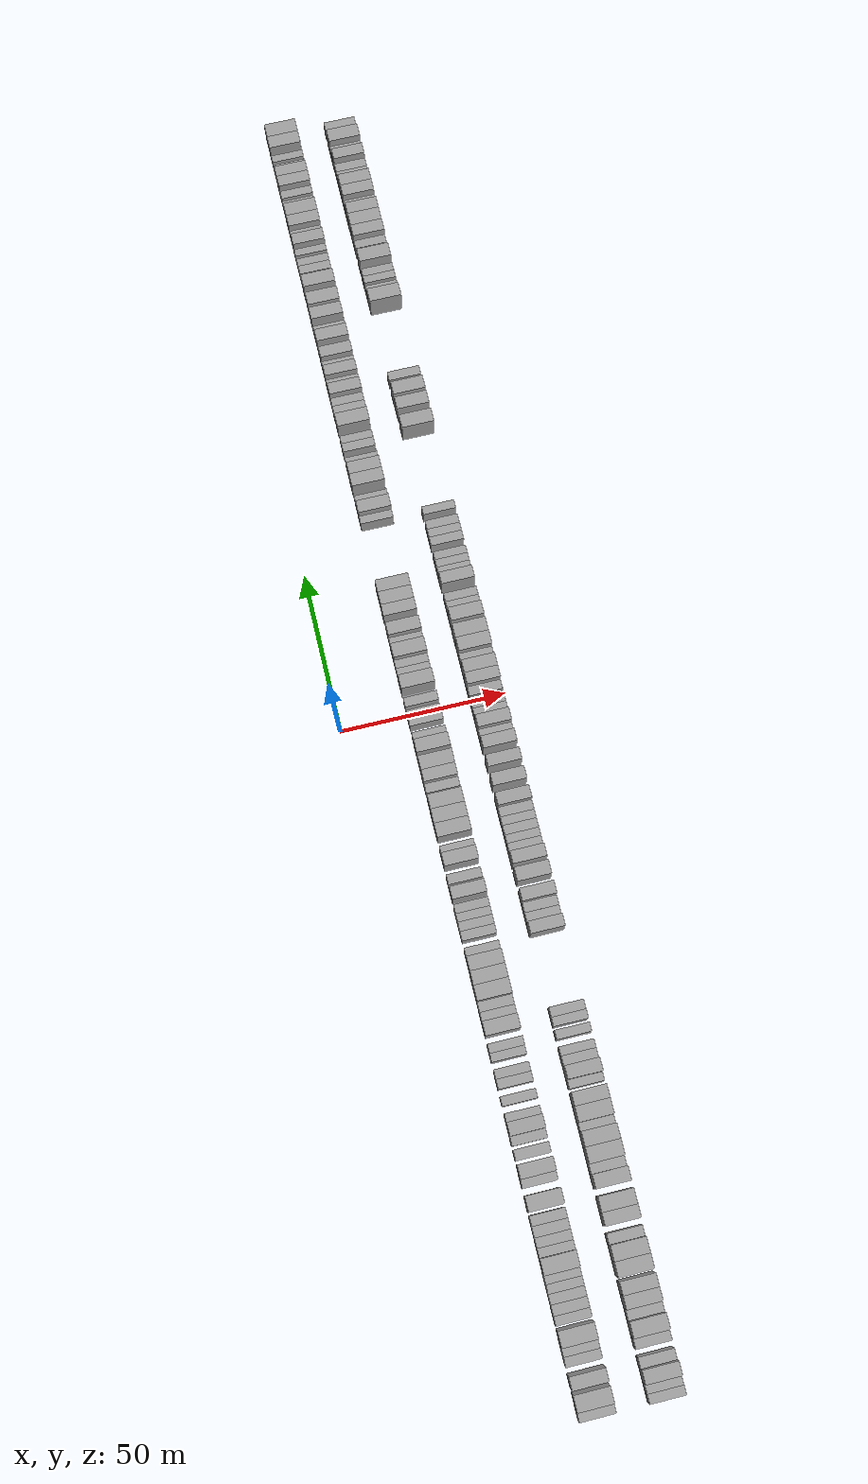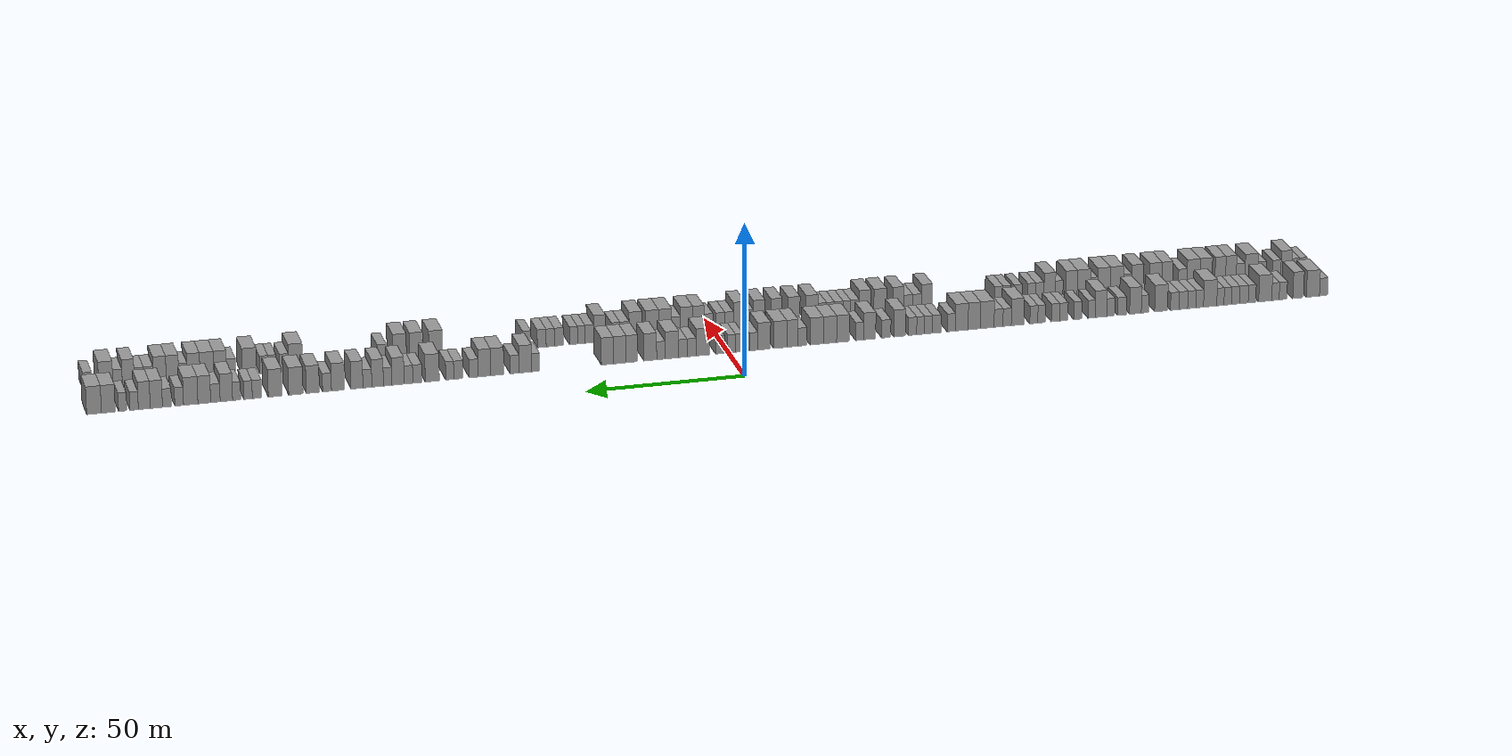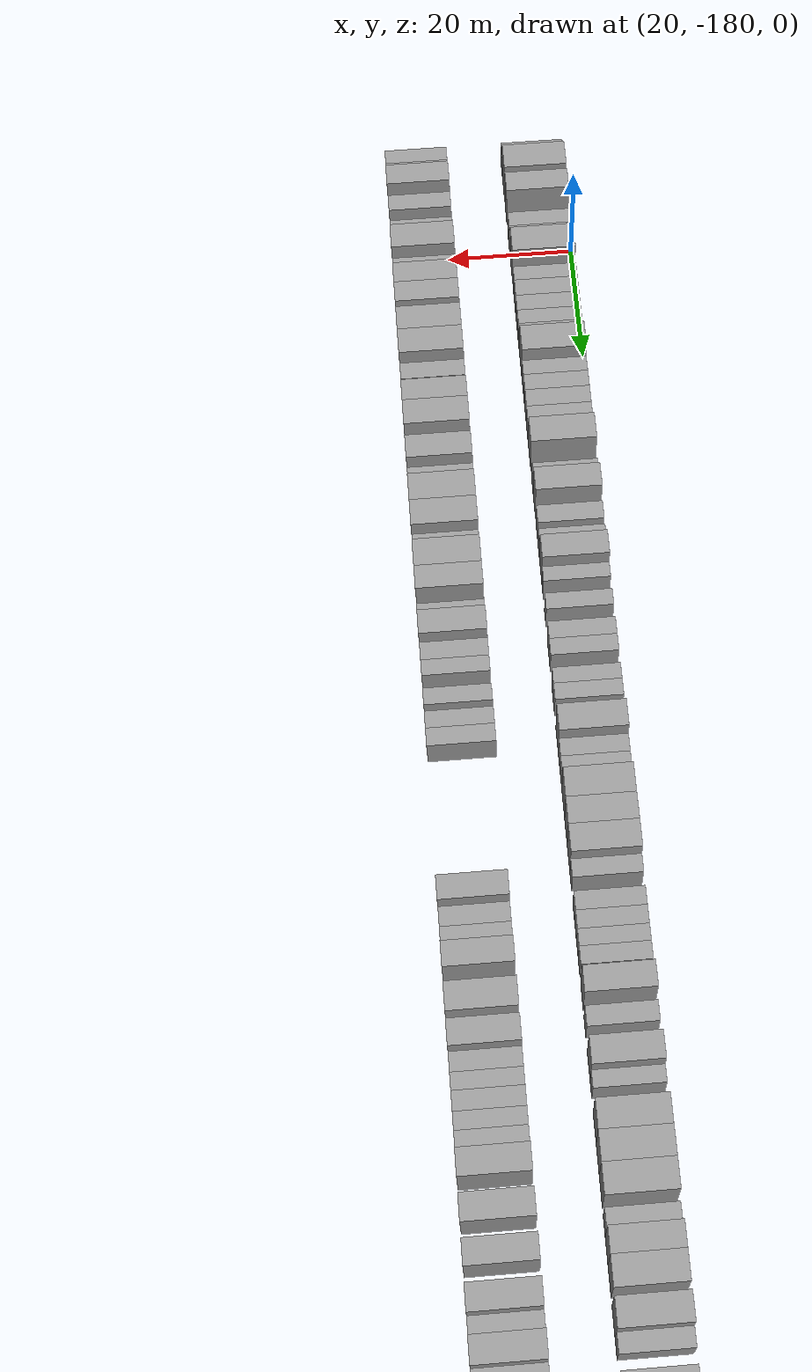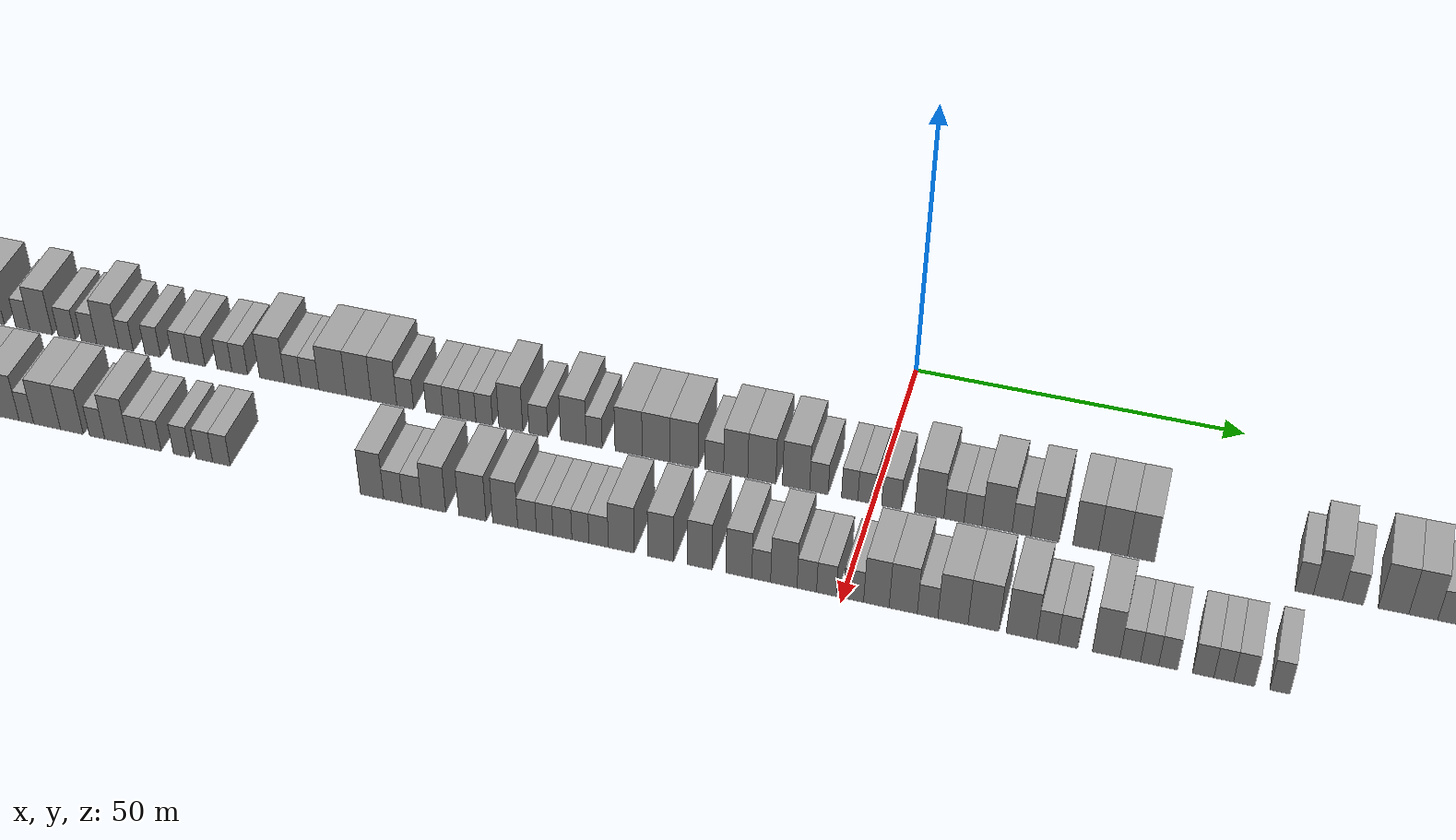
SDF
<sdf version="1.6">
 <world name="default">
  <scene>
   <sky><clouds><speed>12</speed></clouds></sky>
   <ambient>0.4 0.4 0.4 1</ambient>
   <background>0.7 0.7 0.7 1</background>
   <shadows>1</shadows>
  </scene>
  <gravity>0 0 -9.8066</gravity>
  <magnetic_field>6e-06 2.3e-05 -4.2e-05</magnetic_field>
  <physics default="0" name="default_physics" type="ode">
   <ode>
    <solver>
     <type>quick</type>
     <iters>10</iters>
     <sor>1.0</sor>
     <use_dynamic_moi_rescaling>0</use_dynamic_moi_rescaling>
    </solver>
    <constraints>
     <cfm>0</cfm>
     <erp>0.2</erp>
     <contact_max_correcting_vel>100</contact_max_correcting_vel>
     <contact_surface_layer>0.001</contact_surface_layer>
    </constraints>
   </ode>
   <max_step_size>0.004</max_step_size>
   <real_time_factor>1</real_time_factor>
   <real_time_update_rate>250</real_time_update_rate>
  </physics>
  <light name="sun" type="directional">
   <pose>0 0 10 0 0 0</pose>
   <diffuse>0.8 0.8 0.8 1</diffuse>
   <specular>0.2 0.2 0.2 1</specular>
   <attenuation>
    <range>1000</range>
    <constant>0.9</constant>
    <linear>0.01</linear>
    <quadratic>0.001</quadratic>
   </attenuation>
   <direction>-0.5 0.1 -0.9</direction>
  </light>
  <model name="building_1">
   <static>1</static>
   <pose>25.0000 -196.6240 0 0.000000 0.000000 0.000000</pose>
   <link name="link">
    <pose>0 0 3.00 0 0 0</pose>
    <collision name="collision"><geometry><box><size>10.0000 2.7521 6.0000</size></box></geometry></collision>
    <visual name="visual">
     <cast_shadows>0</cast_shadows>
     <geometry><box><size>10.0000 2.7521 6.0000</size></box></geometry>
     <material>
      <script>
       <uri>model://grey_wall/materials/scripts</uri>
       <uri>model://grey_wall/materials/textures</uri>
       <name>vrc/grey_wall</name>
      </script>
     </material>
    </visual>
   </link>
  </model>
  <model name="building_2">
   <static>1</static>
   <pose>25.0000 -193.0271 0 0.000000 0.000000 0.000000</pose>
   <link name="link">
    <pose>0 0 4.50 0 0 0</pose>
    <collision name="collision"><geometry><box><size>10.0000 4.4416 9.0000</size></box></geometry></collision>
    <visual name="visual">
     <cast_shadows>0</cast_shadows>
     <geometry><box><size>10.0000 4.4416 9.0000</size></box></geometry>
     <material>
      <script>
       <uri>model://grey_wall/materials/scripts</uri>
       <uri>model://grey_wall/materials/textures</uri>
       <name>vrc/grey_wall</name>
      </script>
     </material>
    </visual>
   </link>
  </model>
  <model name="building_3">
   <static>1</static>
   <pose>25.0000 -188.0052 0 0.000000 0.000000 0.000000</pose>
   <link name="link">
    <pose>0 0 4.50 0 0 0</pose>
    <collision name="collision"><geometry><box><size>10.0000 3.6023 9.0000</size></box></geometry></collision>
    <visual name="visual">
     <cast_shadows>0</cast_shadows>
     <geometry><box><size>10.0000 3.6023 9.0000</size></box></geometry>
     <material>
      <script>
       <uri>model://grey_wall/materials/scripts</uri>
       <uri>model://grey_wall/materials/textures</uri>
       <name>vrc/grey_wall</name>
      </script>
     </material>
    </visual>
   </link>
  </model>
  <model name="building_4">
   <static>1</static>
   <pose>25.0000 -182.8903 0 0.000000 0.000000 0.000000</pose>
   <link name="link">
    <pose>0 0 3.00 0 0 0</pose>
    <collision name="collision"><geometry><box><size>10.0000 2.6275 6.0000</size></box></geometry></collision>
    <visual name="visual">
     <cast_shadows>0</cast_shadows>
     <geometry><box><size>10.0000 2.6275 6.0000</size></box></geometry>
     <material>
      <script>
       <uri>model://grey_wall/materials/scripts</uri>
       <uri>model://grey_wall/materials/textures</uri>
       <name>vrc/grey_wall</name>
      </script>
     </material>
    </visual>
   </link>
  </model>
  <model name="building_5">
   <static>1</static>
   <pose>25.0000 -180.3268 0 0.000000 0.000000 0.000000</pose>
   <link name="link">
    <pose>0 0 3.00 0 0 0</pose>
    <collision name="collision"><geometry><box><size>10.0000 2.4995 6.0000</size></box></geometry></collision>
    <visual name="visual">
     <cast_shadows>0</cast_shadows>
     <geometry><box><size>10.0000 2.4995 6.0000</size></box></geometry>
     <material>
      <script>
       <uri>model://grey_wall/materials/scripts</uri>
       <uri>model://grey_wall/materials/textures</uri>
       <name>vrc/grey_wall</name>
      </script>
     </material>
    </visual>
   </link>
  </model>
  <model name="building_6">
   <static>1</static>
   <pose>25.0000 -176.8723 0 0.000000 0.000000 0.000000</pose>
   <link name="link">
    <pose>0 0 4.50 0 0 0</pose>
    <collision name="collision"><geometry><box><size>10.0000 4.4094 9.0000</size></box></geometry></collision>
    <visual name="visual">
     <cast_shadows>0</cast_shadows>
     <geometry><box><size>10.0000 4.4094 9.0000</size></box></geometry>
     <material>
      <script>
       <uri>model://grey_wall/materials/scripts</uri>
       <uri>model://grey_wall/materials/textures</uri>
       <name>vrc/grey_wall</name>
      </script>
     </material>
    </visual>
   </link>
  </model>
  <model name="building_7">
   <static>1</static>
   <pose>25.0000 -172.3986 0 0.000000 0.000000 0.000000</pose>
   <link name="link">
    <pose>0 0 3.00 0 0 0</pose>
    <collision name="collision"><geometry><box><size>10.0000 2.5380 6.0000</size></box></geometry></collision>
    <visual name="visual">
     <cast_shadows>0</cast_shadows>
     <geometry><box><size>10.0000 2.5380 6.0000</size></box></geometry>
     <material>
      <script>
       <uri>model://grey_wall/materials/scripts</uri>
       <uri>model://grey_wall/materials/textures</uri>
       <name>vrc/grey_wall</name>
      </script>
     </material>
    </visual>
   </link>
  </model>
  <model name="building_8">
   <static>1</static>
   <pose>25.0000 -169.6750 0 0.000000 0.000000 0.000000</pose>
   <link name="link">
    <pose>0 0 3.00 0 0 0</pose>
    <collision name="collision"><geometry><box><size>10.0000 2.9092 6.0000</size></box></geometry></collision>
    <visual name="visual">
     <cast_shadows>0</cast_shadows>
     <geometry><box><size>10.0000 2.9092 6.0000</size></box></geometry>
     <material>
      <script>
       <uri>model://grey_wall/materials/scripts</uri>
       <uri>model://grey_wall/materials/textures</uri>
       <name>vrc/grey_wall</name>
      </script>
     </material>
    </visual>
   </link>
  </model>
  <model name="building_9">
   <static>1</static>
   <pose>25.0000 -166.8359 0 0.000000 0.000000 0.000000</pose>
   <link name="link">
    <pose>0 0 3.00 0 0 0</pose>
    <collision name="collision"><geometry><box><size>10.0000 2.7690 6.0000</size></box></geometry></collision>
    <visual name="visual">
     <cast_shadows>0</cast_shadows>
     <geometry><box><size>10.0000 2.7690 6.0000</size></box></geometry>
     <material>
      <script>
       <uri>model://grey_wall/materials/scripts</uri>
       <uri>model://grey_wall/materials/textures</uri>
       <name>vrc/grey_wall</name>
      </script>
     </material>
    </visual>
   </link>
  </model>
  <model name="building_10">
   <static>1</static>
   <pose>25.0000 -164.1963 0 0.000000 0.000000 0.000000</pose>
   <link name="link">
    <pose>0 0 3.00 0 0 0</pose>
    <collision name="collision"><geometry><box><size>10.0000 2.5103 6.0000</size></box></geometry></collision>
    <visual name="visual">
     <cast_shadows>0</cast_shadows>
     <geometry><box><size>10.0000 2.5103 6.0000</size></box></geometry>
     <material>
      <script>
       <uri>model://grey_wall/materials/scripts</uri>
       <uri>model://grey_wall/materials/textures</uri>
       <name>vrc/grey_wall</name>
      </script>
     </material>
    </visual>
   </link>
  </model>
  <model name="building_11">
   <static>1</static>
   <pose>25.0000 -161.7370 0 0.000000 0.000000 0.000000</pose>
   <link name="link">
    <pose>0 0 3.00 0 0 0</pose>
    <collision name="collision"><geometry><box><size>10.0000 2.4083 6.0000</size></box></geometry></collision>
    <visual name="visual">
     <cast_shadows>0</cast_shadows>
     <geometry><box><size>10.0000 2.4083 6.0000</size></box></geometry>
     <material>
      <script>
       <uri>model://grey_wall/materials/scripts</uri>
       <uri>model://grey_wall/materials/textures</uri>
       <name>vrc/grey_wall</name>
      </script>
     </material>
    </visual>
   </link>
  </model>
  <model name="building_12">
   <static>1</static>
   <pose>25.0000 -158.3071 0 0.000000 0.000000 0.000000</pose>
   <link name="link">
    <pose>0 0 4.50 0 0 0</pose>
    <collision name="collision"><geometry><box><size>10.0000 4.4516 9.0000</size></box></geometry></collision>
    <visual name="visual">
     <cast_shadows>0</cast_shadows>
     <geometry><box><size>10.0000 4.4516 9.0000</size></box></geometry>
     <material>
      <script>
       <uri>model://grey_wall/materials/scripts</uri>
       <uri>model://grey_wall/materials/textures</uri>
       <name>vrc/grey_wall</name>
      </script>
     </material>
    </visual>
   </link>
  </model>
  <model name="building_13">
   <static>1</static>
   <pose>25.0000 -154.7965 0 0.000000 0.000000 0.000000</pose>
   <link name="link">
    <pose>0 0 3.00 0 0 0</pose>
    <collision name="collision"><geometry><box><size>10.0000 2.5695 6.0000</size></box></geometry></collision>
    <visual name="visual">
     <cast_shadows>0</cast_shadows>
     <geometry><box><size>10.0000 2.5695 6.0000</size></box></geometry>
     <material>
      <script>
       <uri>model://grey_wall/materials/scripts</uri>
       <uri>model://grey_wall/materials/textures</uri>
       <name>vrc/grey_wall</name>
      </script>
     </material>
    </visual>
   </link>
  </model>
  <model name="building_14">
   <static>1</static>
   <pose>25.0000 -152.1294 0 0.000000 0.000000 0.000000</pose>
   <link name="link">
    <pose>0 0 3.00 0 0 0</pose>
    <collision name="collision"><geometry><box><size>10.0000 2.7647 6.0000</size></box></geometry></collision>
    <visual name="visual">
     <cast_shadows>0</cast_shadows>
     <geometry><box><size>10.0000 2.7647 6.0000</size></box></geometry>
     <material>
      <script>
       <uri>model://grey_wall/materials/scripts</uri>
       <uri>model://grey_wall/materials/textures</uri>
       <name>vrc/grey_wall</name>
      </script>
     </material>
    </visual>
   </link>
  </model>
  <model name="building_15">
   <static>1</static>
   <pose>25.0000 -149.2659 0 0.000000 0.000000 0.000000</pose>
   <link name="link">
    <pose>0 0 3.00 0 0 0</pose>
    <collision name="collision"><geometry><box><size>10.0000 2.9622 6.0000</size></box></geometry></collision>
    <visual name="visual">
     <cast_shadows>0</cast_shadows>
     <geometry><box><size>10.0000 2.9622 6.0000</size></box></geometry>
     <material>
      <script>
       <uri>model://grey_wall/materials/scripts</uri>
       <uri>model://grey_wall/materials/textures</uri>
       <name>vrc/grey_wall</name>
      </script>
     </material>
    </visual>
   </link>
  </model>
  <model name="building_16">
   <static>1</static>
   <pose>25.0000 -146.3856 0 0.000000 0.000000 0.000000</pose>
   <link name="link">
    <pose>0 0 3.00 0 0 0</pose>
    <collision name="collision"><geometry><box><size>10.0000 2.7983 6.0000</size></box></geometry></collision>
    <visual name="visual">
     <cast_shadows>0</cast_shadows>
     <geometry><box><size>10.0000 2.7983 6.0000</size></box></geometry>
     <material>
      <script>
       <uri>model://grey_wall/materials/scripts</uri>
       <uri>model://grey_wall/materials/textures</uri>
       <name>vrc/grey_wall</name>
      </script>
     </material>
    </visual>
   </link>
  </model>
  <model name="building_17">
   <static>1</static>
   <pose>25.0000 -141.8396 0 0.000000 0.000000 0.000000</pose>
   <link name="link">
    <pose>0 0 4.50 0 0 0</pose>
    <collision name="collision"><geometry><box><size>10.0000 4.2937 9.0000</size></box></geometry></collision>
    <visual name="visual">
     <cast_shadows>0</cast_shadows>
     <geometry><box><size>10.0000 4.2937 9.0000</size></box></geometry>
     <material>
      <script>
       <uri>model://grey_wall/materials/scripts</uri>
       <uri>model://grey_wall/materials/textures</uri>
       <name>vrc/grey_wall</name>
      </script>
     </material>
    </visual>
   </link>
  </model>
  <model name="building_18">
   <static>1</static>
   <pose>25.0000 -136.4568 0 0.000000 0.000000 0.000000</pose>
   <link name="link">
    <pose>0 0 3.00 0 0 0</pose>
    <collision name="collision"><geometry><box><size>10.0000 2.4720 6.0000</size></box></geometry></collision>
    <visual name="visual">
     <cast_shadows>0</cast_shadows>
     <geometry><box><size>10.0000 2.4720 6.0000</size></box></geometry>
     <material>
      <script>
       <uri>model://grey_wall/materials/scripts</uri>
       <uri>model://grey_wall/materials/textures</uri>
       <name>vrc/grey_wall</name>
      </script>
     </material>
    </visual>
   </link>
  </model>
  <model name="building_19">
   <static>1</static>
   <pose>25.0000 -133.2652 0 0.000000 0.000000 0.000000</pose>
   <link name="link">
    <pose>0 0 4.50 0 0 0</pose>
    <collision name="collision"><geometry><box><size>10.0000 3.9112 9.0000</size></box></geometry></collision>
    <visual name="visual">
     <cast_shadows>0</cast_shadows>
     <geometry><box><size>10.0000 3.9112 9.0000</size></box></geometry>
     <material>
      <script>
       <uri>model://grey_wall/materials/scripts</uri>
       <uri>model://grey_wall/materials/textures</uri>
       <name>vrc/grey_wall</name>
      </script>
     </material>
    </visual>
   </link>
  </model>
  <model name="building_20">
   <static>1</static>
   <pose>25.0000 -128.8170 0 0.000000 0.000000 0.000000</pose>
   <link name="link">
    <pose>0 0 3.00 0 0 0</pose>
    <collision name="collision"><geometry><box><size>10.0000 2.9850 6.0000</size></box></geometry></collision>
    <visual name="visual">
     <cast_shadows>0</cast_shadows>
     <geometry><box><size>10.0000 2.9850 6.0000</size></box></geometry>
     <material>
      <script>
       <uri>model://grey_wall/materials/scripts</uri>
       <uri>model://grey_wall/materials/textures</uri>
       <name>vrc/grey_wall</name>
      </script>
     </material>
    </visual>
   </link>
  </model>
  <model name="building_21">
   <static>1</static>
   <pose>25.0000 -125.0087 0 0.000000 0.000000 0.000000</pose>
   <link name="link">
    <pose>0 0 3.00 0 0 0</pose>
    <collision name="collision"><geometry><box><size>10.0000 2.6317 6.0000</size></box></geometry></collision>
    <visual name="visual">
     <cast_shadows>0</cast_shadows>
     <geometry><box><size>10.0000 2.6317 6.0000</size></box></geometry>
     <material>
      <script>
       <uri>model://grey_wall/materials/scripts</uri>
       <uri>model://grey_wall/materials/textures</uri>
       <name>vrc/grey_wall</name>
      </script>
     </material>
    </visual>
   </link>
  </model>
  <model name="building_22">
   <static>1</static>
   <pose>25.0000 -121.7836 0 0.000000 0.000000 0.000000</pose>
   <link name="link">
    <pose>0 0 4.50 0 0 0</pose>
    <collision name="collision"><geometry><box><size>10.0000 3.8185 9.0000</size></box></geometry></collision>
    <visual name="visual">
     <cast_shadows>0</cast_shadows>
     <geometry><box><size>10.0000 3.8185 9.0000</size></box></geometry>
     <material>
      <script>
       <uri>model://grey_wall/materials/scripts</uri>
       <uri>model://grey_wall/materials/textures</uri>
       <name>vrc/grey_wall</name>
      </script>
     </material>
    </visual>
   </link>
  </model>
  <model name="building_23">
   <static>1</static>
   <pose>25.0000 -118.6639 0 0.000000 0.000000 0.000000</pose>
   <link name="link">
    <pose>0 0 3.00 0 0 0</pose>
    <collision name="collision"><geometry><box><size>10.0000 2.4210 6.0000</size></box></geometry></collision>
    <visual name="visual">
     <cast_shadows>0</cast_shadows>
     <geometry><box><size>10.0000 2.4210 6.0000</size></box></geometry>
     <material>
      <script>
       <uri>model://grey_wall/materials/scripts</uri>
       <uri>model://grey_wall/materials/textures</uri>
       <name>vrc/grey_wall</name>
      </script>
     </material>
    </visual>
   </link>
  </model>
  <model name="building_24">
   <static>1</static>
   <pose>25.0000 -114.1288 0 0.000000 0.000000 0.000000</pose>
   <link name="link">
    <pose>0 0 3.00 0 0 0</pose>
    <collision name="collision"><geometry><box><size>10.0000 2.6491 6.0000</size></box></geometry></collision>
    <visual name="visual">
     <cast_shadows>0</cast_shadows>
     <geometry><box><size>10.0000 2.6491 6.0000</size></box></geometry>
     <material>
      <script>
       <uri>model://grey_wall/materials/scripts</uri>
       <uri>model://grey_wall/materials/textures</uri>
       <name>vrc/grey_wall</name>
      </script>
     </material>
    </visual>
   </link>
  </model>
  <model name="building_25">
   <static>1</static>
   <pose>25.0000 -109.4126 0 0.000000 0.000000 0.000000</pose>
   <link name="link">
    <pose>0 0 3.00 0 0 0</pose>
    <collision name="collision"><geometry><box><size>10.0000 2.7834 6.0000</size></box></geometry></collision>
    <visual name="visual">
     <cast_shadows>0</cast_shadows>
     <geometry><box><size>10.0000 2.7834 6.0000</size></box></geometry>
     <material>
      <script>
       <uri>model://grey_wall/materials/scripts</uri>
       <uri>model://grey_wall/materials/textures</uri>
       <name>vrc/grey_wall</name>
      </script>
     </material>
    </visual>
   </link>
  </model>
  <model name="building_26">
   <static>1</static>
   <pose>25.0000 -106.6699 0 0.000000 0.000000 0.000000</pose>
   <link name="link">
    <pose>0 0 3.00 0 0 0</pose>
    <collision name="collision"><geometry><box><size>10.0000 2.7020 6.0000</size></box></geometry></collision>
    <visual name="visual">
     <cast_shadows>0</cast_shadows>
     <geometry><box><size>10.0000 2.7020 6.0000</size></box></geometry>
     <material>
      <script>
       <uri>model://grey_wall/materials/scripts</uri>
       <uri>model://grey_wall/materials/textures</uri>
       <name>vrc/grey_wall</name>
      </script>
     </material>
    </visual>
   </link>
  </model>
  <model name="building_27">
   <static>1</static>
   <pose>25.0000 -102.0671 0 0.000000 0.000000 0.000000</pose>
   <link name="link">
    <pose>0 0 3.00 0 0 0</pose>
    <collision name="collision"><geometry><box><size>10.0000 2.5036 6.0000</size></box></geometry></collision>
    <visual name="visual">
     <cast_shadows>0</cast_shadows>
     <geometry><box><size>10.0000 2.5036 6.0000</size></box></geometry>
     <material>
      <script>
       <uri>model://grey_wall/materials/scripts</uri>
       <uri>model://grey_wall/materials/textures</uri>
       <name>vrc/grey_wall</name>
      </script>
     </material>
    </visual>
   </link>
  </model>
  <model name="building_28">
   <static>1</static>
   <pose>25.0000 -99.5092 0 0.000000 0.000000 0.000000</pose>
   <link name="link">
    <pose>0 0 3.00 0 0 0</pose>
    <collision name="collision"><geometry><box><size>10.0000 2.6123 6.0000</size></box></geometry></collision>
    <visual name="visual">
     <cast_shadows>0</cast_shadows>
     <geometry><box><size>10.0000 2.6123 6.0000</size></box></geometry>
     <material>
      <script>
       <uri>model://grey_wall/materials/scripts</uri>
       <uri>model://grey_wall/materials/textures</uri>
       <name>vrc/grey_wall</name>
      </script>
     </material>
    </visual>
   </link>
  </model>
  <model name="building_29">
   <static>1</static>
   <pose>25.0000 -94.1316 0 0.000000 0.000000 0.000000</pose>
   <link name="link">
    <pose>0 0 4.50 0 0 0</pose>
    <collision name="collision"><geometry><box><size>10.0000 4.1430 9.0000</size></box></geometry></collision>
    <visual name="visual">
     <cast_shadows>0</cast_shadows>
     <geometry><box><size>10.0000 4.1430 9.0000</size></box></geometry>
     <material>
      <script>
       <uri>model://grey_wall/materials/scripts</uri>
       <uri>model://grey_wall/materials/textures</uri>
       <name>vrc/grey_wall</name>
      </script>
     </material>
    </visual>
   </link>
  </model>
  <model name="building_30">
   <static>1</static>
   <pose>25.0000 -90.6957 0 0.000000 0.000000 0.000000</pose>
   <link name="link">
    <pose>0 0 3.00 0 0 0</pose>
    <collision name="collision"><geometry><box><size>10.0000 2.7287 6.0000</size></box></geometry></collision>
    <visual name="visual">
     <cast_shadows>0</cast_shadows>
     <geometry><box><size>10.0000 2.7287 6.0000</size></box></geometry>
     <material>
      <script>
       <uri>model://grey_wall/materials/scripts</uri>
       <uri>model://grey_wall/materials/textures</uri>
       <name>vrc/grey_wall</name>
      </script>
     </material>
    </visual>
   </link>
  </model>
  <model name="building_31">
   <static>1</static>
   <pose>25.0000 -87.8668 0 0.000000 0.000000 0.000000</pose>
   <link name="link">
    <pose>0 0 3.00 0 0 0</pose>
    <collision name="collision"><geometry><box><size>10.0000 2.9290 6.0000</size></box></geometry></collision>
    <visual name="visual">
     <cast_shadows>0</cast_shadows>
     <geometry><box><size>10.0000 2.9290 6.0000</size></box></geometry>
     <material>
      <script>
       <uri>model://grey_wall/materials/scripts</uri>
       <uri>model://grey_wall/materials/textures</uri>
       <name>vrc/grey_wall</name>
      </script>
     </material>
    </visual>
   </link>
  </model>
  <model name="building_32">
   <static>1</static>
   <pose>25.0000 -84.1582 0 0.000000 0.000000 0.000000</pose>
   <link name="link">
    <pose>0 0 4.50 0 0 0</pose>
    <collision name="collision"><geometry><box><size>10.0000 4.4882 9.0000</size></box></geometry></collision>
    <visual name="visual">
     <cast_shadows>0</cast_shadows>
     <geometry><box><size>10.0000 4.4882 9.0000</size></box></geometry>
     <material>
      <script>
       <uri>model://grey_wall/materials/scripts</uri>
       <uri>model://grey_wall/materials/textures</uri>
       <name>vrc/grey_wall</name>
      </script>
     </material>
    </visual>
   </link>
  </model>
  <model name="building_33">
   <static>1</static>
   <pose>25.0000 -79.8913 0 0.000000 0.000000 0.000000</pose>
   <link name="link">
    <pose>0 0 4.50 0 0 0</pose>
    <collision name="collision"><geometry><box><size>10.0000 4.0456 9.0000</size></box></geometry></collision>
    <visual name="visual">
     <cast_shadows>0</cast_shadows>
     <geometry><box><size>10.0000 4.0456 9.0000</size></box></geometry>
     <material>
      <script>
       <uri>model://grey_wall/materials/scripts</uri>
       <uri>model://grey_wall/materials/textures</uri>
       <name>vrc/grey_wall</name>
      </script>
     </material>
    </visual>
   </link>
  </model>
  <model name="building_34">
   <static>1</static>
   <pose>25.0000 -75.7905 0 0.000000 0.000000 0.000000</pose>
   <link name="link">
    <pose>0 0 4.50 0 0 0</pose>
    <collision name="collision"><geometry><box><size>10.0000 4.1559 9.0000</size></box></geometry></collision>
    <visual name="visual">
     <cast_shadows>0</cast_shadows>
     <geometry><box><size>10.0000 4.1559 9.0000</size></box></geometry>
     <material>
      <script>
       <uri>model://grey_wall/materials/scripts</uri>
       <uri>model://grey_wall/materials/textures</uri>
       <name>vrc/grey_wall</name>
      </script>
     </material>
    </visual>
   </link>
  </model>
  <model name="building_35">
   <static>1</static>
   <pose>25.0000 -72.3466 0 0.000000 0.000000 0.000000</pose>
   <link name="link">
    <pose>0 0 3.00 0 0 0</pose>
    <collision name="collision"><geometry><box><size>10.0000 2.7320 6.0000</size></box></geometry></collision>
    <visual name="visual">
     <cast_shadows>0</cast_shadows>
     <geometry><box><size>10.0000 2.7320 6.0000</size></box></geometry>
     <material>
      <script>
       <uri>model://grey_wall/materials/scripts</uri>
       <uri>model://grey_wall/materials/textures</uri>
       <name>vrc/grey_wall</name>
      </script>
     </material>
    </visual>
   </link>
  </model>
  <model name="building_36">
   <static>1</static>
   <pose>25.0000 -67.5896 0 0.000000 0.000000 0.000000</pose>
   <link name="link">
    <pose>0 0 3.00 0 0 0</pose>
    <collision name="collision"><geometry><box><size>10.0000 2.7820 6.0000</size></box></geometry></collision>
    <visual name="visual">
     <cast_shadows>0</cast_shadows>
     <geometry><box><size>10.0000 2.7820 6.0000</size></box></geometry>
     <material>
      <script>
       <uri>model://grey_wall/materials/scripts</uri>
       <uri>model://grey_wall/materials/textures</uri>
       <name>vrc/grey_wall</name>
      </script>
     </material>
    </visual>
   </link>
  </model>
  <model name="building_37">
   <static>1</static>
   <pose>25.0000 -64.8409 0 0.000000 0.000000 0.000000</pose>
   <link name="link">
    <pose>0 0 3.00 0 0 0</pose>
    <collision name="collision"><geometry><box><size>10.0000 2.7154 6.0000</size></box></geometry></collision>
    <visual name="visual">
     <cast_shadows>0</cast_shadows>
     <geometry><box><size>10.0000 2.7154 6.0000</size></box></geometry>
     <material>
      <script>
       <uri>model://grey_wall/materials/scripts</uri>
       <uri>model://grey_wall/materials/textures</uri>
       <name>vrc/grey_wall</name>
      </script>
     </material>
    </visual>
   </link>
  </model>
  <model name="building_38">
   <static>1</static>
   <pose>25.0000 -62.2412 0 0.000000 0.000000 0.000000</pose>
   <link name="link">
    <pose>0 0 3.00 0 0 0</pose>
    <collision name="collision"><geometry><box><size>10.0000 2.4840 6.0000</size></box></geometry></collision>
    <visual name="visual">
     <cast_shadows>0</cast_shadows>
     <geometry><box><size>10.0000 2.4840 6.0000</size></box></geometry>
     <material>
      <script>
       <uri>model://grey_wall/materials/scripts</uri>
       <uri>model://grey_wall/materials/textures</uri>
       <name>vrc/grey_wall</name>
      </script>
     </material>
    </visual>
   </link>
  </model>
  <model name="building_39">
   <static>1</static>
   <pose>25.0000 -59.6701 0 0.000000 0.000000 0.000000</pose>
   <link name="link">
    <pose>0 0 3.00 0 0 0</pose>
    <collision name="collision"><geometry><box><size>10.0000 2.6581 6.0000</size></box></geometry></collision>
    <visual name="visual">
     <cast_shadows>0</cast_shadows>
     <geometry><box><size>10.0000 2.6581 6.0000</size></box></geometry>
     <material>
      <script>
       <uri>model://grey_wall/materials/scripts</uri>
       <uri>model://grey_wall/materials/textures</uri>
       <name>vrc/grey_wall</name>
      </script>
     </material>
    </visual>
   </link>
  </model>
  <model name="building_40">
   <static>1</static>
   <pose>25.0000 -55.4458 0 0.000000 0.000000 0.000000</pose>
   <link name="link">
    <pose>0 0 4.50 0 0 0</pose>
    <collision name="collision"><geometry><box><size>10.0000 3.7904 9.0000</size></box></geometry></collision>
    <visual name="visual">
     <cast_shadows>0</cast_shadows>
     <geometry><box><size>10.0000 3.7904 9.0000</size></box></geometry>
     <material>
      <script>
       <uri>model://grey_wall/materials/scripts</uri>
       <uri>model://grey_wall/materials/textures</uri>
       <name>vrc/grey_wall</name>
      </script>
     </material>
    </visual>
   </link>
  </model>
  <model name="building_41">
   <static>1</static>
   <pose>25.0000 -51.0784 0 0.000000 0.000000 0.000000</pose>
   <link name="link">
    <pose>0 0 3.00 0 0 0</pose>
    <collision name="collision"><geometry><box><size>10.0000 2.9444 6.0000</size></box></geometry></collision>
    <visual name="visual">
     <cast_shadows>0</cast_shadows>
     <geometry><box><size>10.0000 2.9444 6.0000</size></box></geometry>
     <material>
      <script>
       <uri>model://grey_wall/materials/scripts</uri>
       <uri>model://grey_wall/materials/textures</uri>
       <name>vrc/grey_wall</name>
      </script>
     </material>
    </visual>
   </link>
  </model>
  <model name="building_42">
   <static>1</static>
   <pose>25.0000 -45.6107 0 0.000000 0.000000 0.000000</pose>
   <link name="link">
    <pose>0 0 4.50 0 0 0</pose>
    <collision name="collision"><geometry><box><size>10.0000 3.9909 9.0000</size></box></geometry></collision>
    <visual name="visual">
     <cast_shadows>0</cast_shadows>
     <geometry><box><size>10.0000 3.9909 9.0000</size></box></geometry>
     <material>
      <script>
       <uri>model://grey_wall/materials/scripts</uri>
       <uri>model://grey_wall/materials/textures</uri>
       <name>vrc/grey_wall</name>
      </script>
     </material>
    </visual>
   </link>
  </model>
  <model name="building_43">
   <static>1</static>
   <pose>25.0000 -42.3640 0 0.000000 0.000000 0.000000</pose>
   <link name="link">
    <pose>0 0 3.00 0 0 0</pose>
    <collision name="collision"><geometry><box><size>10.0000 2.5026 6.0000</size></box></geometry></collision>
    <visual name="visual">
     <cast_shadows>0</cast_shadows>
     <geometry><box><size>10.0000 2.5026 6.0000</size></box></geometry>
     <material>
      <script>
       <uri>model://grey_wall/materials/scripts</uri>
       <uri>model://grey_wall/materials/textures</uri>
       <name>vrc/grey_wall</name>
      </script>
     </material>
    </visual>
   </link>
  </model>
  <model name="building_44">
   <static>1</static>
   <pose>25.0000 -37.0086 0 0.000000 0.000000 0.000000</pose>
   <link name="link">
    <pose>0 0 4.50 0 0 0</pose>
    <collision name="collision"><geometry><box><size>10.0000 4.2082 9.0000</size></box></geometry></collision>
    <visual name="visual">
     <cast_shadows>0</cast_shadows>
     <geometry><box><size>10.0000 4.2082 9.0000</size></box></geometry>
     <material>
      <script>
       <uri>model://grey_wall/materials/scripts</uri>
       <uri>model://grey_wall/materials/textures</uri>
       <name>vrc/grey_wall</name>
      </script>
     </material>
    </visual>
   </link>
  </model>
  <model name="building_45">
   <static>1</static>
   <pose>25.0000 -32.7683 0 0.000000 0.000000 0.000000</pose>
   <link name="link">
    <pose>0 0 4.50 0 0 0</pose>
    <collision name="collision"><geometry><box><size>10.0000 4.2723 9.0000</size></box></geometry></collision>
    <visual name="visual">
     <cast_shadows>0</cast_shadows>
     <geometry><box><size>10.0000 4.2723 9.0000</size></box></geometry>
     <material>
      <script>
       <uri>model://grey_wall/materials/scripts</uri>
       <uri>model://grey_wall/materials/textures</uri>
       <name>vrc/grey_wall</name>
      </script>
     </material>
    </visual>
   </link>
  </model>
  <model name="building_46">
   <static>1</static>
   <pose>25.0000 -28.4604 0 0.000000 0.000000 0.000000</pose>
   <link name="link">
    <pose>0 0 4.50 0 0 0</pose>
    <collision name="collision"><geometry><box><size>10.0000 4.3434 9.0000</size></box></geometry></collision>
    <visual name="visual">
     <cast_shadows>0</cast_shadows>
     <geometry><box><size>10.0000 4.3434 9.0000</size></box></geometry>
     <material>
      <script>
       <uri>model://grey_wall/materials/scripts</uri>
       <uri>model://grey_wall/materials/textures</uri>
       <name>vrc/grey_wall</name>
      </script>
     </material>
    </visual>
   </link>
  </model>
  <model name="building_47">
   <static>1</static>
   <pose>25.0000 -23.8618 0 0.000000 0.000000 0.000000</pose>
   <link name="link">
    <pose>0 0 3.00 0 0 0</pose>
    <collision name="collision"><geometry><box><size>10.0000 2.8538 6.0000</size></box></geometry></collision>
    <visual name="visual">
     <cast_shadows>0</cast_shadows>
     <geometry><box><size>10.0000 2.8538 6.0000</size></box></geometry>
     <material>
      <script>
       <uri>model://grey_wall/materials/scripts</uri>
       <uri>model://grey_wall/materials/textures</uri>
       <name>vrc/grey_wall</name>
      </script>
     </material>
    </visual>
   </link>
  </model>
  <model name="building_48">
   <static>1</static>
   <pose>25.0000 -20.6068 0 0.000000 0.000000 0.000000</pose>
   <link name="link">
    <pose>0 0 4.50 0 0 0</pose>
    <collision name="collision"><geometry><box><size>10.0000 3.6561 9.0000</size></box></geometry></collision>
    <visual name="visual">
     <cast_shadows>0</cast_shadows>
     <geometry><box><size>10.0000 3.6561 9.0000</size></box></geometry>
     <material>
      <script>
       <uri>model://grey_wall/materials/scripts</uri>
       <uri>model://grey_wall/materials/textures</uri>
       <name>vrc/grey_wall</name>
      </script>
     </material>
    </visual>
   </link>
  </model>
  <model name="building_49">
   <static>1</static>
   <pose>25.0000 -16.6605 0 0.000000 0.000000 0.000000</pose>
   <link name="link">
    <pose>0 0 4.50 0 0 0</pose>
    <collision name="collision"><geometry><box><size>10.0000 4.2365 9.0000</size></box></geometry></collision>
    <visual name="visual">
     <cast_shadows>0</cast_shadows>
     <geometry><box><size>10.0000 4.2365 9.0000</size></box></geometry>
     <material>
      <script>
       <uri>model://grey_wall/materials/scripts</uri>
       <uri>model://grey_wall/materials/textures</uri>
       <name>vrc/grey_wall</name>
      </script>
     </material>
    </visual>
   </link>
  </model>
  <model name="building_50">
   <static>1</static>
   <pose>25.0000 -11.5001 0 0.000000 0.000000 0.000000</pose>
   <link name="link">
    <pose>0 0 4.50 0 0 0</pose>
    <collision name="collision"><geometry><box><size>10.0000 4.0843 9.0000</size></box></geometry></collision>
    <visual name="visual">
     <cast_shadows>0</cast_shadows>
     <geometry><box><size>10.0000 4.0843 9.0000</size></box></geometry>
     <material>
      <script>
       <uri>model://grey_wall/materials/scripts</uri>
       <uri>model://grey_wall/materials/textures</uri>
       <name>vrc/grey_wall</name>
      </script>
     </material>
    </visual>
   </link>
  </model>
  <model name="building_51">
   <static>1</static>
   <pose>25.0000 -8.0746 0 0.000000 0.000000 0.000000</pose>
   <link name="link">
    <pose>0 0 3.00 0 0 0</pose>
    <collision name="collision"><geometry><box><size>10.0000 2.7667 6.0000</size></box></geometry></collision>
    <visual name="visual">
     <cast_shadows>0</cast_shadows>
     <geometry><box><size>10.0000 2.7667 6.0000</size></box></geometry>
     <material>
      <script>
       <uri>model://grey_wall/materials/scripts</uri>
       <uri>model://grey_wall/materials/textures</uri>
       <name>vrc/grey_wall</name>
      </script>
     </material>
    </visual>
   </link>
  </model>
  <model name="building_52">
   <static>1</static>
   <pose>25.0000 -3.4818 0 0.000000 0.000000 0.000000</pose>
   <link name="link">
    <pose>0 0 3.00 0 0 0</pose>
    <collision name="collision"><geometry><box><size>10.0000 2.4187 6.0000</size></box></geometry></collision>
    <visual name="visual">
     <cast_shadows>0</cast_shadows>
     <geometry><box><size>10.0000 2.4187 6.0000</size></box></geometry>
     <material>
      <script>
       <uri>model://grey_wall/materials/scripts</uri>
       <uri>model://grey_wall/materials/textures</uri>
       <name>vrc/grey_wall</name>
      </script>
     </material>
    </visual>
   </link>
  </model>
  <model name="building_53">
   <static>1</static>
   <pose>25.0000 -1.0128 0 0.000000 0.000000 0.000000</pose>
   <link name="link">
    <pose>0 0 3.00 0 0 0</pose>
    <collision name="collision"><geometry><box><size>10.0000 2.5193 6.0000</size></box></geometry></collision>
    <visual name="visual">
     <cast_shadows>0</cast_shadows>
     <geometry><box><size>10.0000 2.5193 6.0000</size></box></geometry>
     <material>
      <script>
       <uri>model://grey_wall/materials/scripts</uri>
       <uri>model://grey_wall/materials/textures</uri>
       <name>vrc/grey_wall</name>
      </script>
     </material>
    </visual>
   </link>
  </model>
  <model name="building_54">
   <static>1</static>
   <pose>25.0000 2.6914 0 0.000000 0.000000 0.000000</pose>
   <link name="link">
    <pose>0 0 3.00 0 0 0</pose>
    <collision name="collision"><geometry><box><size>10.0000 2.8892 6.0000</size></box></geometry></collision>
    <visual name="visual">
     <cast_shadows>0</cast_shadows>
     <geometry><box><size>10.0000 2.8892 6.0000</size></box></geometry>
     <material>
      <script>
       <uri>model://grey_wall/materials/scripts</uri>
       <uri>model://grey_wall/materials/textures</uri>
       <name>vrc/grey_wall</name>
      </script>
     </material>
    </visual>
   </link>
  </model>
  <model name="building_55">
   <static>1</static>
   <pose>25.0000 8.2709 0 0.000000 0.000000 0.000000</pose>
   <link name="link">
    <pose>0 0 4.50 0 0 0</pose>
    <collision name="collision"><geometry><box><size>10.0000 4.2698 9.0000</size></box></geometry></collision>
    <visual name="visual">
     <cast_shadows>0</cast_shadows>
     <geometry><box><size>10.0000 4.2698 9.0000</size></box></geometry>
     <material>
      <script>
       <uri>model://grey_wall/materials/scripts</uri>
       <uri>model://grey_wall/materials/textures</uri>
       <name>vrc/grey_wall</name>
      </script>
     </material>
    </visual>
   </link>
  </model>
  <model name="building_56">
   <static>1</static>
   <pose>25.0000 11.8664 0 0.000000 0.000000 0.000000</pose>
   <link name="link">
    <pose>0 0 3.00 0 0 0</pose>
    <collision name="collision"><geometry><box><size>10.0000 2.9211 6.0000</size></box></geometry></collision>
    <visual name="visual">
     <cast_shadows>0</cast_shadows>
     <geometry><box><size>10.0000 2.9211 6.0000</size></box></geometry>
     <material>
      <script>
       <uri>model://grey_wall/materials/scripts</uri>
       <uri>model://grey_wall/materials/textures</uri>
       <name>vrc/grey_wall</name>
      </script>
     </material>
    </visual>
   </link>
  </model>
  <model name="building_57">
   <static>1</static>
   <pose>25.0000 14.6334 0 0.000000 0.000000 0.000000</pose>
   <link name="link">
    <pose>0 0 3.00 0 0 0</pose>
    <collision name="collision"><geometry><box><size>10.0000 2.6130 6.0000</size></box></geometry></collision>
    <visual name="visual">
     <cast_shadows>0</cast_shadows>
     <geometry><box><size>10.0000 2.6130 6.0000</size></box></geometry>
     <material>
      <script>
       <uri>model://grey_wall/materials/scripts</uri>
       <uri>model://grey_wall/materials/textures</uri>
       <name>vrc/grey_wall</name>
      </script>
     </material>
    </visual>
   </link>
  </model>
  <model name="building_58">
   <static>1</static>
   <pose>25.0000 18.1228 0 0.000000 0.000000 0.000000</pose>
   <link name="link">
    <pose>0 0 4.50 0 0 0</pose>
    <collision name="collision"><geometry><box><size>10.0000 4.3657 9.0000</size></box></geometry></collision>
    <visual name="visual">
     <cast_shadows>0</cast_shadows>
     <geometry><box><size>10.0000 4.3657 9.0000</size></box></geometry>
     <material>
      <script>
       <uri>model://grey_wall/materials/scripts</uri>
       <uri>model://grey_wall/materials/textures</uri>
       <name>vrc/grey_wall</name>
      </script>
     </material>
    </visual>
   </link>
  </model>
  <model name="building_59">
   <static>1</static>
   <pose>25.0000 21.6638 0 0.000000 0.000000 0.000000</pose>
   <link name="link">
    <pose>0 0 3.00 0 0 0</pose>
    <collision name="collision"><geometry><box><size>10.0000 2.7163 6.0000</size></box></geometry></collision>
    <visual name="visual">
     <cast_shadows>0</cast_shadows>
     <geometry><box><size>10.0000 2.7163 6.0000</size></box></geometry>
     <material>
      <script>
       <uri>model://grey_wall/materials/scripts</uri>
       <uri>model://grey_wall/materials/textures</uri>
       <name>vrc/grey_wall</name>
      </script>
     </material>
    </visual>
   </link>
  </model>
  <model name="building_60">
   <static>1</static>
   <pose>25.0000 25.0352 0 0.000000 0.000000 0.000000</pose>
   <link name="link">
    <pose>0 0 4.50 0 0 0</pose>
    <collision name="collision"><geometry><box><size>10.0000 4.0266 9.0000</size></box></geometry></collision>
    <visual name="visual">
     <cast_shadows>0</cast_shadows>
     <geometry><box><size>10.0000 4.0266 9.0000</size></box></geometry>
     <material>
      <script>
       <uri>model://grey_wall/materials/scripts</uri>
       <uri>model://grey_wall/materials/textures</uri>
       <name>vrc/grey_wall</name>
      </script>
     </material>
    </visual>
   </link>
  </model>
  <model name="building_61">
   <static>1</static>
   <pose>25.0000 30.8770 0 0.000000 0.000000 0.000000</pose>
   <link name="link">
    <pose>0 0 4.50 0 0 0</pose>
    <collision name="collision"><geometry><box><size>10.0000 3.6570 9.0000</size></box></geometry></collision>
    <visual name="visual">
     <cast_shadows>0</cast_shadows>
     <geometry><box><size>10.0000 3.6570 9.0000</size></box></geometry>
     <material>
      <script>
       <uri>model://grey_wall/materials/scripts</uri>
       <uri>model://grey_wall/materials/textures</uri>
       <name>vrc/grey_wall</name>
      </script>
     </material>
    </visual>
   </link>
  </model>
  <model name="building_62">
   <static>1</static>
   <pose>25.0000 34.7551 0 0.000000 0.000000 0.000000</pose>
   <link name="link">
    <pose>0 0 4.50 0 0 0</pose>
    <collision name="collision"><geometry><box><size>10.0000 4.0992 9.0000</size></box></geometry></collision>
    <visual name="visual">
     <cast_shadows>0</cast_shadows>
     <geometry><box><size>10.0000 4.0992 9.0000</size></box></geometry>
     <material>
      <script>
       <uri>model://grey_wall/materials/scripts</uri>
       <uri>model://grey_wall/materials/textures</uri>
       <name>vrc/grey_wall</name>
      </script>
     </material>
    </visual>
   </link>
  </model>
  <model name="building_63">
   <static>1</static>
   <pose>25.0000 38.7124 0 0.000000 0.000000 0.000000</pose>
   <link name="link">
    <pose>0 0 4.50 0 0 0</pose>
    <collision name="collision"><geometry><box><size>10.0000 3.8153 9.0000</size></box></geometry></collision>
    <visual name="visual">
     <cast_shadows>0</cast_shadows>
     <geometry><box><size>10.0000 3.8153 9.0000</size></box></geometry>
     <material>
      <script>
       <uri>model://grey_wall/materials/scripts</uri>
       <uri>model://grey_wall/materials/textures</uri>
       <name>vrc/grey_wall</name>
      </script>
     </material>
    </visual>
   </link>
  </model>
  <model name="building_64">
   <static>1</static>
   <pose>25.0000 61.4079 0 0.000000 0.000000 0.000000</pose>
   <link name="link">
    <pose>0 0 3.00 0 0 0</pose>
    <collision name="collision"><geometry><box><size>10.0000 2.5252 6.0000</size></box></geometry></collision>
    <visual name="visual">
     <cast_shadows>0</cast_shadows>
     <geometry><box><size>10.0000 2.5252 6.0000</size></box></geometry>
     <material>
      <script>
       <uri>model://grey_wall/materials/scripts</uri>
       <uri>model://grey_wall/materials/textures</uri>
       <name>vrc/grey_wall</name>
      </script>
     </material>
    </visual>
   </link>
  </model>
  <model name="building_65">
   <static>1</static>
   <pose>25.0000 64.6402 0 0.000000 0.000000 0.000000</pose>
   <link name="link">
    <pose>0 0 4.50 0 0 0</pose>
    <collision name="collision"><geometry><box><size>10.0000 3.9393 9.0000</size></box></geometry></collision>
    <visual name="visual">
     <cast_shadows>0</cast_shadows>
     <geometry><box><size>10.0000 3.9393 9.0000</size></box></geometry>
     <material>
      <script>
       <uri>model://grey_wall/materials/scripts</uri>
       <uri>model://grey_wall/materials/textures</uri>
       <name>vrc/grey_wall</name>
      </script>
     </material>
    </visual>
   </link>
  </model>
  <model name="building_66">
   <static>1</static>
   <pose>25.0000 68.0581 0 0.000000 0.000000 0.000000</pose>
   <link name="link">
    <pose>0 0 3.00 0 0 0</pose>
    <collision name="collision"><geometry><box><size>10.0000 2.8966 6.0000</size></box></geometry></collision>
    <visual name="visual">
     <cast_shadows>0</cast_shadows>
     <geometry><box><size>10.0000 2.8966 6.0000</size></box></geometry>
     <material>
      <script>
       <uri>model://grey_wall/materials/scripts</uri>
       <uri>model://grey_wall/materials/textures</uri>
       <name>vrc/grey_wall</name>
      </script>
     </material>
    </visual>
   </link>
  </model>
  <model name="building_67">
   <static>1</static>
   <pose>25.0000 73.5662 0 0.000000 0.000000 0.000000</pose>
   <link name="link">
    <pose>0 0 4.50 0 0 0</pose>
    <collision name="collision"><geometry><box><size>10.0000 4.1196 9.0000</size></box></geometry></collision>
    <visual name="visual">
     <cast_shadows>0</cast_shadows>
     <geometry><box><size>10.0000 4.1196 9.0000</size></box></geometry>
     <material>
      <script>
       <uri>model://grey_wall/materials/scripts</uri>
       <uri>model://grey_wall/materials/textures</uri>
       <name>vrc/grey_wall</name>
      </script>
     </material>
    </visual>
   </link>
  </model>
  <model name="building_68">
   <static>1</static>
   <pose>25.0000 77.5588 0 0.000000 0.000000 0.000000</pose>
   <link name="link">
    <pose>0 0 4.50 0 0 0</pose>
    <collision name="collision"><geometry><box><size>10.0000 3.8657 9.0000</size></box></geometry></collision>
    <visual name="visual">
     <cast_shadows>0</cast_shadows>
     <geometry><box><size>10.0000 3.8657 9.0000</size></box></geometry>
     <material>
      <script>
       <uri>model://grey_wall/materials/scripts</uri>
       <uri>model://grey_wall/materials/textures</uri>
       <name>vrc/grey_wall</name>
      </script>
     </material>
    </visual>
   </link>
  </model>
  <model name="building_69">
   <static>1</static>
   <pose>25.0000 80.9182 0 0.000000 0.000000 0.000000</pose>
   <link name="link">
    <pose>0 0 3.00 0 0 0</pose>
    <collision name="collision"><geometry><box><size>10.0000 2.8530 6.0000</size></box></geometry></collision>
    <visual name="visual">
     <cast_shadows>0</cast_shadows>
     <geometry><box><size>10.0000 2.8530 6.0000</size></box></geometry>
     <material>
      <script>
       <uri>model://grey_wall/materials/scripts</uri>
       <uri>model://grey_wall/materials/textures</uri>
       <name>vrc/grey_wall</name>
      </script>
     </material>
    </visual>
   </link>
  </model>
  <model name="building_70">
   <static>1</static>
   <pose>25.0000 85.7758 0 0.000000 0.000000 0.000000</pose>
   <link name="link">
    <pose>0 0 3.00 0 0 0</pose>
    <collision name="collision"><geometry><box><size>10.0000 2.8622 6.0000</size></box></geometry></collision>
    <visual name="visual">
     <cast_shadows>0</cast_shadows>
     <geometry><box><size>10.0000 2.8622 6.0000</size></box></geometry>
     <material>
      <script>
       <uri>model://grey_wall/materials/scripts</uri>
       <uri>model://grey_wall/materials/textures</uri>
       <name>vrc/grey_wall</name>
      </script>
     </material>
    </visual>
   </link>
  </model>
  <model name="building_71">
   <static>1</static>
   <pose>25.0000 88.4623 0 0.000000 0.000000 0.000000</pose>
   <link name="link">
    <pose>0 0 3.00 0 0 0</pose>
    <collision name="collision"><geometry><box><size>10.0000 2.5108 6.0000</size></box></geometry></collision>
    <visual name="visual">
     <cast_shadows>0</cast_shadows>
     <geometry><box><size>10.0000 2.5108 6.0000</size></box></geometry>
     <material>
      <script>
       <uri>model://grey_wall/materials/scripts</uri>
       <uri>model://grey_wall/materials/textures</uri>
       <name>vrc/grey_wall</name>
      </script>
     </material>
    </visual>
   </link>
  </model>
  <model name="building_72">
   <static>1</static>
   <pose>25.0000 93.9240 0 0.000000 0.000000 0.000000</pose>
   <link name="link">
    <pose>0 0 4.50 0 0 0</pose>
    <collision name="collision"><geometry><box><size>10.0000 4.4126 9.0000</size></box></geometry></collision>
    <visual name="visual">
     <cast_shadows>0</cast_shadows>
     <geometry><box><size>10.0000 4.4126 9.0000</size></box></geometry>
     <material>
      <script>
       <uri>model://grey_wall/materials/scripts</uri>
       <uri>model://grey_wall/materials/textures</uri>
       <name>vrc/grey_wall</name>
      </script>
     </material>
    </visual>
   </link>
  </model>
  <model name="building_73">
   <static>1</static>
   <pose>25.0000 98.5716 0 0.000000 0.000000 0.000000</pose>
   <link name="link">
    <pose>0 0 3.00 0 0 0</pose>
    <collision name="collision"><geometry><box><size>10.0000 2.8826 6.0000</size></box></geometry></collision>
    <visual name="visual">
     <cast_shadows>0</cast_shadows>
     <geometry><box><size>10.0000 2.8826 6.0000</size></box></geometry>
     <material>
      <script>
       <uri>model://grey_wall/materials/scripts</uri>
       <uri>model://grey_wall/materials/textures</uri>
       <name>vrc/grey_wall</name>
      </script>
     </material>
    </visual>
   </link>
  </model>
  <model name="building_74">
   <static>1</static>
   <pose>25.0000 101.3755 0 0.000000 0.000000 0.000000</pose>
   <link name="link">
    <pose>0 0 3.00 0 0 0</pose>
    <collision name="collision"><geometry><box><size>10.0000 2.7252 6.0000</size></box></geometry></collision>
    <visual name="visual">
     <cast_shadows>0</cast_shadows>
     <geometry><box><size>10.0000 2.7252 6.0000</size></box></geometry>
     <material>
      <script>
       <uri>model://grey_wall/materials/scripts</uri>
       <uri>model://grey_wall/materials/textures</uri>
       <name>vrc/grey_wall</name>
      </script>
     </material>
    </visual>
   </link>
  </model>
  <model name="building_75">
   <static>1</static>
   <pose>25.0000 104.6256 0 0.000000 0.000000 0.000000</pose>
   <link name="link">
    <pose>0 0 4.50 0 0 0</pose>
    <collision name="collision"><geometry><box><size>10.0000 3.7750 9.0000</size></box></geometry></collision>
    <visual name="visual">
     <cast_shadows>0</cast_shadows>
     <geometry><box><size>10.0000 3.7750 9.0000</size></box></geometry>
     <material>
      <script>
       <uri>model://grey_wall/materials/scripts</uri>
       <uri>model://grey_wall/materials/textures</uri>
       <name>vrc/grey_wall</name>
      </script>
     </material>
    </visual>
   </link>
  </model>
  <model name="building_76">
   <static>1</static>
   <pose>25.0000 107.8437 0 0.000000 0.000000 0.000000</pose>
   <link name="link">
    <pose>0 0 3.00 0 0 0</pose>
    <collision name="collision"><geometry><box><size>10.0000 2.6613 6.0000</size></box></geometry></collision>
    <visual name="visual">
     <cast_shadows>0</cast_shadows>
     <geometry><box><size>10.0000 2.6613 6.0000</size></box></geometry>
     <material>
      <script>
       <uri>model://grey_wall/materials/scripts</uri>
       <uri>model://grey_wall/materials/textures</uri>
       <name>vrc/grey_wall</name>
      </script>
     </material>
    </visual>
   </link>
  </model>
  <model name="building_77">
   <static>1</static>
   <pose>25.0000 110.9807 0 0.000000 0.000000 0.000000</pose>
   <link name="link">
    <pose>0 0 4.50 0 0 0</pose>
    <collision name="collision"><geometry><box><size>10.0000 3.6126 9.0000</size></box></geometry></collision>
    <visual name="visual">
     <cast_shadows>0</cast_shadows>
     <geometry><box><size>10.0000 3.6126 9.0000</size></box></geometry>
     <material>
      <script>
       <uri>model://grey_wall/materials/scripts</uri>
       <uri>model://grey_wall/materials/textures</uri>
       <name>vrc/grey_wall</name>
      </script>
     </material>
    </visual>
   </link>
  </model>
  <model name="building_78">
   <static>1</static>
   <pose>25.0000 114.1705 0 0.000000 0.000000 0.000000</pose>
   <link name="link">
    <pose>0 0 3.00 0 0 0</pose>
    <collision name="collision"><geometry><box><size>10.0000 2.7669 6.0000</size></box></geometry></collision>
    <visual name="visual">
     <cast_shadows>0</cast_shadows>
     <geometry><box><size>10.0000 2.7669 6.0000</size></box></geometry>
     <material>
      <script>
       <uri>model://grey_wall/materials/scripts</uri>
       <uri>model://grey_wall/materials/textures</uri>
       <name>vrc/grey_wall</name>
      </script>
     </material>
    </visual>
   </link>
  </model>
  <model name="building_79">
   <static>1</static>
   <pose>25.0000 117.4091 0 0.000000 0.000000 0.000000</pose>
   <link name="link">
    <pose>0 0 4.50 0 0 0</pose>
    <collision name="collision"><geometry><box><size>10.0000 3.7104 9.0000</size></box></geometry></collision>
    <visual name="visual">
     <cast_shadows>0</cast_shadows>
     <geometry><box><size>10.0000 3.7104 9.0000</size></box></geometry>
     <material>
      <script>
       <uri>model://grey_wall/materials/scripts</uri>
       <uri>model://grey_wall/materials/textures</uri>
       <name>vrc/grey_wall</name>
      </script>
     </material>
    </visual>
   </link>
  </model>
  <model name="building_80">
   <static>1</static>
   <pose>25.0000 123.2911 0 0.000000 0.000000 0.000000</pose>
   <link name="link">
    <pose>0 0 4.50 0 0 0</pose>
    <collision name="collision"><geometry><box><size>10.0000 4.0536 9.0000</size></box></geometry></collision>
    <visual name="visual">
     <cast_shadows>0</cast_shadows>
     <geometry><box><size>10.0000 4.0536 9.0000</size></box></geometry>
     <material>
      <script>
       <uri>model://grey_wall/materials/scripts</uri>
       <uri>model://grey_wall/materials/textures</uri>
       <name>vrc/grey_wall</name>
      </script>
     </material>
    </visual>
   </link>
  </model>
  <model name="building_81">
   <static>1</static>
   <pose>25.0000 126.6876 0 0.000000 0.000000 0.000000</pose>
   <link name="link">
    <pose>0 0 3.00 0 0 0</pose>
    <collision name="collision"><geometry><box><size>10.0000 2.7394 6.0000</size></box></geometry></collision>
    <visual name="visual">
     <cast_shadows>0</cast_shadows>
     <geometry><box><size>10.0000 2.7394 6.0000</size></box></geometry>
     <material>
      <script>
       <uri>model://grey_wall/materials/scripts</uri>
       <uri>model://grey_wall/materials/textures</uri>
       <name>vrc/grey_wall</name>
      </script>
     </material>
    </visual>
   </link>
  </model>
  <model name="building_82">
   <static>1</static>
   <pose>25.0000 131.0903 0 0.000000 0.000000 0.000000</pose>
   <link name="link">
    <pose>0 0 4.50 0 0 0</pose>
    <collision name="collision"><geometry><box><size>10.0000 4.0660 9.0000</size></box></geometry></collision>
    <visual name="visual">
     <cast_shadows>0</cast_shadows>
     <geometry><box><size>10.0000 4.0660 9.0000</size></box></geometry>
     <material>
      <script>
       <uri>model://grey_wall/materials/scripts</uri>
       <uri>model://grey_wall/materials/textures</uri>
       <name>vrc/grey_wall</name>
      </script>
     </material>
    </visual>
   </link>
  </model>
  <model name="building_83">
   <static>1</static>
   <pose>25.0000 136.3307 0 0.000000 0.000000 0.000000</pose>
   <link name="link">
    <pose>0 0 4.50 0 0 0</pose>
    <collision name="collision"><geometry><box><size>10.0000 4.4148 9.0000</size></box></geometry></collision>
    <visual name="visual">
     <cast_shadows>0</cast_shadows>
     <geometry><box><size>10.0000 4.4148 9.0000</size></box></geometry>
     <material>
      <script>
       <uri>model://grey_wall/materials/scripts</uri>
       <uri>model://grey_wall/materials/textures</uri>
       <name>vrc/grey_wall</name>
      </script>
     </material>
    </visual>
   </link>
  </model>
  <model name="building_84">
   <static>1</static>
   <pose>25.0000 142.6915 0 0.000000 0.000000 0.000000</pose>
   <link name="link">
    <pose>0 0 4.50 0 0 0</pose>
    <collision name="collision"><geometry><box><size>10.0000 4.3068 9.0000</size></box></geometry></collision>
    <visual name="visual">
     <cast_shadows>0</cast_shadows>
     <geometry><box><size>10.0000 4.3068 9.0000</size></box></geometry>
     <material>
      <script>
       <uri>model://grey_wall/materials/scripts</uri>
       <uri>model://grey_wall/materials/textures</uri>
       <name>vrc/grey_wall</name>
      </script>
     </material>
    </visual>
   </link>
  </model>
  <model name="building_85">
   <static>1</static>
   <pose>25.0000 148.2996 0 0.000000 0.000000 0.000000</pose>
   <link name="link">
    <pose>0 0 3.00 0 0 0</pose>
    <collision name="collision"><geometry><box><size>10.0000 2.9093 6.0000</size></box></geometry></collision>
    <visual name="visual">
     <cast_shadows>0</cast_shadows>
     <geometry><box><size>10.0000 2.9093 6.0000</size></box></geometry>
     <material>
      <script>
       <uri>model://grey_wall/materials/scripts</uri>
       <uri>model://grey_wall/materials/textures</uri>
       <name>vrc/grey_wall</name>
      </script>
     </material>
    </visual>
   </link>
  </model>
  <model name="building_86">
   <static>1</static>
   <pose>25.0000 151.0538 0 0.000000 0.000000 0.000000</pose>
   <link name="link">
    <pose>0 0 3.00 0 0 0</pose>
    <collision name="collision"><geometry><box><size>10.0000 2.5992 6.0000</size></box></geometry></collision>
    <visual name="visual">
     <cast_shadows>0</cast_shadows>
     <geometry><box><size>10.0000 2.5992 6.0000</size></box></geometry>
     <material>
      <script>
       <uri>model://grey_wall/materials/scripts</uri>
       <uri>model://grey_wall/materials/textures</uri>
       <name>vrc/grey_wall</name>
      </script>
     </material>
    </visual>
   </link>
  </model>
  <model name="building_87">
   <static>1</static>
   <pose>25.0000 154.5870 0 0.000000 0.000000 0.000000</pose>
   <link name="link">
    <pose>0 0 3.00 0 0 0</pose>
    <collision name="collision"><geometry><box><size>10.0000 2.4672 6.0000</size></box></geometry></collision>
    <visual name="visual">
     <cast_shadows>0</cast_shadows>
     <geometry><box><size>10.0000 2.4672 6.0000</size></box></geometry>
     <material>
      <script>
       <uri>model://grey_wall/materials/scripts</uri>
       <uri>model://grey_wall/materials/textures</uri>
       <name>vrc/grey_wall</name>
      </script>
     </material>
    </visual>
   </link>
  </model>
  <model name="building_88">
   <static>1</static>
   <pose>25.0000 157.7297 0 0.000000 0.000000 0.000000</pose>
   <link name="link">
    <pose>0 0 4.50 0 0 0</pose>
    <collision name="collision"><geometry><box><size>10.0000 3.8180 9.0000</size></box></geometry></collision>
    <visual name="visual">
     <cast_shadows>0</cast_shadows>
     <geometry><box><size>10.0000 3.8180 9.0000</size></box></geometry>
     <material>
      <script>
       <uri>model://grey_wall/materials/scripts</uri>
       <uri>model://grey_wall/materials/textures</uri>
       <name>vrc/grey_wall</name>
      </script>
     </material>
    </visual>
   </link>
  </model>
  <model name="building_89">
   <static>1</static>
   <pose>25.0000 161.0930 0 0.000000 0.000000 0.000000</pose>
   <link name="link">
    <pose>0 0 3.00 0 0 0</pose>
    <collision name="collision"><geometry><box><size>10.0000 2.9086 6.0000</size></box></geometry></collision>
    <visual name="visual">
     <cast_shadows>0</cast_shadows>
     <geometry><box><size>10.0000 2.9086 6.0000</size></box></geometry>
     <material>
      <script>
       <uri>model://grey_wall/materials/scripts</uri>
       <uri>model://grey_wall/materials/textures</uri>
       <name>vrc/grey_wall</name>
      </script>
     </material>
    </visual>
   </link>
  </model>
  <model name="building_90">
   <static>1</static>
   <pose>25.0000 164.5099 0 0.000000 0.000000 0.000000</pose>
   <link name="link">
    <pose>0 0 4.50 0 0 0</pose>
    <collision name="collision"><geometry><box><size>10.0000 3.9251 9.0000</size></box></geometry></collision>
    <visual name="visual">
     <cast_shadows>0</cast_shadows>
     <geometry><box><size>10.0000 3.9251 9.0000</size></box></geometry>
     <material>
      <script>
       <uri>model://grey_wall/materials/scripts</uri>
       <uri>model://grey_wall/materials/textures</uri>
       <name>vrc/grey_wall</name>
      </script>
     </material>
    </visual>
   </link>
  </model>
  <model name="building_91">
   <static>1</static>
   <pose>25.0000 168.6640 0 0.000000 0.000000 0.000000</pose>
   <link name="link">
    <pose>0 0 4.50 0 0 0</pose>
    <collision name="collision"><geometry><box><size>10.0000 4.3831 9.0000</size></box></geometry></collision>
    <visual name="visual">
     <cast_shadows>0</cast_shadows>
     <geometry><box><size>10.0000 4.3831 9.0000</size></box></geometry>
     <material>
      <script>
       <uri>model://grey_wall/materials/scripts</uri>
       <uri>model://grey_wall/materials/textures</uri>
       <name>vrc/grey_wall</name>
      </script>
     </material>
    </visual>
   </link>
  </model>
  <model name="building_92">
   <static>1</static>
   <pose>25.0000 172.1884 0 0.000000 0.000000 0.000000</pose>
   <link name="link">
    <pose>0 0 3.00 0 0 0</pose>
    <collision name="collision"><geometry><box><size>10.0000 2.6658 6.0000</size></box></geometry></collision>
    <visual name="visual">
     <cast_shadows>0</cast_shadows>
     <geometry><box><size>10.0000 2.6658 6.0000</size></box></geometry>
     <material>
      <script>
       <uri>model://grey_wall/materials/scripts</uri>
       <uri>model://grey_wall/materials/textures</uri>
       <name>vrc/grey_wall</name>
      </script>
     </material>
    </visual>
   </link>
  </model>
  <model name="building_93">
   <static>1</static>
   <pose>25.0000 175.9110 0 0.000000 0.000000 0.000000</pose>
   <link name="link">
    <pose>0 0 3.00 0 0 0</pose>
    <collision name="collision"><geometry><box><size>10.0000 2.7793 6.0000</size></box></geometry></collision>
    <visual name="visual">
     <cast_shadows>0</cast_shadows>
     <geometry><box><size>10.0000 2.7793 6.0000</size></box></geometry>
     <material>
      <script>
       <uri>model://grey_wall/materials/scripts</uri>
       <uri>model://grey_wall/materials/textures</uri>
       <name>vrc/grey_wall</name>
      </script>
     </material>
    </visual>
   </link>
  </model>
  <model name="building_94">
   <static>1</static>
   <pose>25.0000 179.1659 0 0.000000 0.000000 0.000000</pose>
   <link name="link">
    <pose>0 0 4.50 0 0 0</pose>
    <collision name="collision"><geometry><box><size>10.0000 3.7306 9.0000</size></box></geometry></collision>
    <visual name="visual">
     <cast_shadows>0</cast_shadows>
     <geometry><box><size>10.0000 3.7306 9.0000</size></box></geometry>
     <material>
      <script>
       <uri>model://grey_wall/materials/scripts</uri>
       <uri>model://grey_wall/materials/textures</uri>
       <name>vrc/grey_wall</name>
      </script>
     </material>
    </visual>
   </link>
  </model>
  <model name="building_95">
   <static>1</static>
   <pose>25.0000 182.8454 0 0.000000 0.000000 0.000000</pose>
   <link name="link">
    <pose>0 0 4.50 0 0 0</pose>
    <collision name="collision"><geometry><box><size>10.0000 3.6283 9.0000</size></box></geometry></collision>
    <visual name="visual">
     <cast_shadows>0</cast_shadows>
     <geometry><box><size>10.0000 3.6283 9.0000</size></box></geometry>
     <material>
      <script>
       <uri>model://grey_wall/materials/scripts</uri>
       <uri>model://grey_wall/materials/textures</uri>
       <name>vrc/grey_wall</name>
      </script>
     </material>
    </visual>
   </link>
  </model>
  <model name="building_96">
   <static>1</static>
   <pose>25.0000 185.9268 0 0.000000 0.000000 0.000000</pose>
   <link name="link">
    <pose>0 0 3.00 0 0 0</pose>
    <collision name="collision"><geometry><box><size>10.0000 2.5345 6.0000</size></box></geometry></collision>
    <visual name="visual">
     <cast_shadows>0</cast_shadows>
     <geometry><box><size>10.0000 2.5345 6.0000</size></box></geometry>
     <material>
      <script>
       <uri>model://grey_wall/materials/scripts</uri>
       <uri>model://grey_wall/materials/textures</uri>
       <name>vrc/grey_wall</name>
      </script>
     </material>
    </visual>
   </link>
  </model>
  <model name="building_97">
   <static>1</static>
   <pose>25.0000 189.4286 0 0.000000 0.000000 0.000000</pose>
   <link name="link">
    <pose>0 0 3.00 0 0 0</pose>
    <collision name="collision"><geometry><box><size>10.0000 2.4690 6.0000</size></box></geometry></collision>
    <visual name="visual">
     <cast_shadows>0</cast_shadows>
     <geometry><box><size>10.0000 2.4690 6.0000</size></box></geometry>
     <material>
      <script>
       <uri>model://grey_wall/materials/scripts</uri>
       <uri>model://grey_wall/materials/textures</uri>
       <name>vrc/grey_wall</name>
      </script>
     </material>
    </visual>
   </link>
  </model>
  <model name="building_98">
   <static>1</static>
   <pose>25.0000 193.7729 0 0.000000 0.000000 0.000000</pose>
   <link name="link">
    <pose>0 0 4.50 0 0 0</pose>
    <collision name="collision"><geometry><box><size>10.0000 4.2197 9.0000</size></box></geometry></collision>
    <visual name="visual">
     <cast_shadows>0</cast_shadows>
     <geometry><box><size>10.0000 4.2197 9.0000</size></box></geometry>
     <material>
      <script>
       <uri>model://grey_wall/materials/scripts</uri>
       <uri>model://grey_wall/materials/textures</uri>
       <name>vrc/grey_wall</name>
      </script>
     </material>
    </visual>
   </link>
  </model>
  <model name="building_99">
   <static>1</static>
   <pose>25.0000 198.1286 0 0.000000 0.000000 0.000000</pose>
   <link name="link">
    <pose>0 0 4.50 0 0 0</pose>
    <collision name="collision"><geometry><box><size>10.0000 4.4916 9.0000</size></box></geometry></collision>
    <visual name="visual">
     <cast_shadows>0</cast_shadows>
     <geometry><box><size>10.0000 4.4916 9.0000</size></box></geometry>
     <material>
      <script>
       <uri>model://grey_wall/materials/scripts</uri>
       <uri>model://grey_wall/materials/textures</uri>
       <name>vrc/grey_wall</name>
      </script>
     </material>
    </visual>
   </link>
  </model>
  <model name="building_100">
   <static>1</static>
   <pose>44.0000 -196.7285 0 0.000000 0.000000 0.000000</pose>
   <link name="link">
    <pose>0 0 3.00 0 0 0</pose>
    <collision name="collision"><geometry><box><size>10.0000 2.5431 6.0000</size></box></geometry></collision>
    <visual name="visual">
     <cast_shadows>0</cast_shadows>
     <geometry><box><size>10.0000 2.5431 6.0000</size></box></geometry>
     <material>
      <script>
       <uri>model://grey_wall/materials/scripts</uri>
       <uri>model://grey_wall/materials/textures</uri>
       <name>vrc/grey_wall</name>
      </script>
     </material>
    </visual>
   </link>
  </model>
  <model name="building_101">
   <static>1</static>
   <pose>44.0000 -194.1441 0 0.000000 0.000000 0.000000</pose>
   <link name="link">
    <pose>0 0 3.00 0 0 0</pose>
    <collision name="collision"><geometry><box><size>10.0000 2.6255 6.0000</size></box></geometry></collision>
    <visual name="visual">
     <cast_shadows>0</cast_shadows>
     <geometry><box><size>10.0000 2.6255 6.0000</size></box></geometry>
     <material>
      <script>
       <uri>model://grey_wall/materials/scripts</uri>
       <uri>model://grey_wall/materials/textures</uri>
       <name>vrc/grey_wall</name>
      </script>
     </material>
    </visual>
   </link>
  </model>
  <model name="building_102">
   <static>1</static>
   <pose>44.0000 -190.9655 0 0.000000 0.000000 0.000000</pose>
   <link name="link">
    <pose>0 0 4.50 0 0 0</pose>
    <collision name="collision"><geometry><box><size>10.0000 3.7317 9.0000</size></box></geometry></collision>
    <visual name="visual">
     <cast_shadows>0</cast_shadows>
     <geometry><box><size>10.0000 3.7317 9.0000</size></box></geometry>
     <material>
      <script>
       <uri>model://grey_wall/materials/scripts</uri>
       <uri>model://grey_wall/materials/textures</uri>
       <name>vrc/grey_wall</name>
      </script>
     </material>
    </visual>
   </link>
  </model>
  <model name="building_103">
   <static>1</static>
   <pose>44.0000 -187.6283 0 0.000000 0.000000 0.000000</pose>
   <link name="link">
    <pose>0 0 3.00 0 0 0</pose>
    <collision name="collision"><geometry><box><size>10.0000 2.9427 6.0000</size></box></geometry></collision>
    <visual name="visual">
     <cast_shadows>0</cast_shadows>
     <geometry><box><size>10.0000 2.9427 6.0000</size></box></geometry>
     <material>
      <script>
       <uri>model://grey_wall/materials/scripts</uri>
       <uri>model://grey_wall/materials/textures</uri>
       <name>vrc/grey_wall</name>
      </script>
     </material>
    </visual>
   </link>
  </model>
  <model name="building_104">
   <static>1</static>
   <pose>44.0000 -182.6684 0 0.000000 0.000000 0.000000</pose>
   <link name="link">
    <pose>0 0 3.00 0 0 0</pose>
    <collision name="collision"><geometry><box><size>10.0000 2.9771 6.0000</size></box></geometry></collision>
    <visual name="visual">
     <cast_shadows>0</cast_shadows>
     <geometry><box><size>10.0000 2.9771 6.0000</size></box></geometry>
     <material>
      <script>
       <uri>model://grey_wall/materials/scripts</uri>
       <uri>model://grey_wall/materials/textures</uri>
       <name>vrc/grey_wall</name>
      </script>
     </material>
    </visual>
   </link>
  </model>
  <model name="building_105">
   <static>1</static>
   <pose>44.0000 -179.0158 0 0.000000 0.000000 0.000000</pose>
   <link name="link">
    <pose>0 0 4.50 0 0 0</pose>
    <collision name="collision"><geometry><box><size>10.0000 4.3281 9.0000</size></box></geometry></collision>
    <visual name="visual">
     <cast_shadows>0</cast_shadows>
     <geometry><box><size>10.0000 4.3281 9.0000</size></box></geometry>
     <material>
      <script>
       <uri>model://grey_wall/materials/scripts</uri>
       <uri>model://grey_wall/materials/textures</uri>
       <name>vrc/grey_wall</name>
      </script>
     </material>
    </visual>
   </link>
  </model>
  <model name="building_106">
   <static>1</static>
   <pose>44.0000 -175.3624 0 0.000000 0.000000 0.000000</pose>
   <link name="link">
    <pose>0 0 3.00 0 0 0</pose>
    <collision name="collision"><geometry><box><size>10.0000 2.9787 6.0000</size></box></geometry></collision>
    <visual name="visual">
     <cast_shadows>0</cast_shadows>
     <geometry><box><size>10.0000 2.9787 6.0000</size></box></geometry>
     <material>
      <script>
       <uri>model://grey_wall/materials/scripts</uri>
       <uri>model://grey_wall/materials/textures</uri>
       <name>vrc/grey_wall</name>
      </script>
     </material>
    </visual>
   </link>
  </model>
  <model name="building_107">
   <static>1</static>
   <pose>44.0000 -172.0548 0 0.000000 0.000000 0.000000</pose>
   <link name="link">
    <pose>0 0 4.50 0 0 0</pose>
    <collision name="collision"><geometry><box><size>10.0000 3.6367 9.0000</size></box></geometry></collision>
    <visual name="visual">
     <cast_shadows>0</cast_shadows>
     <geometry><box><size>10.0000 3.6367 9.0000</size></box></geometry>
     <material>
      <script>
       <uri>model://grey_wall/materials/scripts</uri>
       <uri>model://grey_wall/materials/textures</uri>
       <name>vrc/grey_wall</name>
      </script>
     </material>
    </visual>
   </link>
  </model>
  <model name="building_108">
   <static>1</static>
   <pose>44.0000 -168.4299 0 0.000000 0.000000 0.000000</pose>
   <link name="link">
    <pose>0 0 4.50 0 0 0</pose>
    <collision name="collision"><geometry><box><size>10.0000 3.6131 9.0000</size></box></geometry></collision>
    <visual name="visual">
     <cast_shadows>0</cast_shadows>
     <geometry><box><size>10.0000 3.6131 9.0000</size></box></geometry>
     <material>
      <script>
       <uri>model://grey_wall/materials/scripts</uri>
       <uri>model://grey_wall/materials/textures</uri>
       <name>vrc/grey_wall</name>
      </script>
     </material>
    </visual>
   </link>
  </model>
  <model name="building_109">
   <static>1</static>
   <pose>44.0000 -163.5489 0 0.000000 0.000000 0.000000</pose>
   <link name="link">
    <pose>0 0 4.50 0 0 0</pose>
    <collision name="collision"><geometry><box><size>10.0000 4.1488 9.0000</size></box></geometry></collision>
    <visual name="visual">
     <cast_shadows>0</cast_shadows>
     <geometry><box><size>10.0000 4.1488 9.0000</size></box></geometry>
     <material>
      <script>
       <uri>model://grey_wall/materials/scripts</uri>
       <uri>model://grey_wall/materials/textures</uri>
       <name>vrc/grey_wall</name>
      </script>
     </material>
    </visual>
   </link>
  </model>
  <model name="building_110">
   <static>1</static>
   <pose>44.0000 -159.3108 0 0.000000 0.000000 0.000000</pose>
   <link name="link">
    <pose>0 0 4.50 0 0 0</pose>
    <collision name="collision"><geometry><box><size>10.0000 4.3276 9.0000</size></box></geometry></collision>
    <visual name="visual">
     <cast_shadows>0</cast_shadows>
     <geometry><box><size>10.0000 4.3276 9.0000</size></box></geometry>
     <material>
      <script>
       <uri>model://grey_wall/materials/scripts</uri>
       <uri>model://grey_wall/materials/textures</uri>
       <name>vrc/grey_wall</name>
      </script>
     </material>
    </visual>
   </link>
  </model>
  <model name="building_111">
   <static>1</static>
   <pose>44.0000 -155.6921 0 0.000000 0.000000 0.000000</pose>
   <link name="link">
    <pose>0 0 3.00 0 0 0</pose>
    <collision name="collision"><geometry><box><size>10.0000 2.9097 6.0000</size></box></geometry></collision>
    <visual name="visual">
     <cast_shadows>0</cast_shadows>
     <geometry><box><size>10.0000 2.9097 6.0000</size></box></geometry>
     <material>
      <script>
       <uri>model://grey_wall/materials/scripts</uri>
       <uri>model://grey_wall/materials/textures</uri>
       <name>vrc/grey_wall</name>
      </script>
     </material>
    </visual>
   </link>
  </model>
  <model name="building_112">
   <static>1</static>
   <pose>44.0000 -150.4291 0 0.000000 0.000000 0.000000</pose>
   <link name="link">
    <pose>0 0 4.50 0 0 0</pose>
    <collision name="collision"><geometry><box><size>10.0000 3.6164 9.0000</size></box></geometry></collision>
    <visual name="visual">
     <cast_shadows>0</cast_shadows>
     <geometry><box><size>10.0000 3.6164 9.0000</size></box></geometry>
     <material>
      <script>
       <uri>model://grey_wall/materials/scripts</uri>
       <uri>model://grey_wall/materials/textures</uri>
       <name>vrc/grey_wall</name>
      </script>
     </material>
    </visual>
   </link>
  </model>
  <model name="building_113">
   <static>1</static>
   <pose>44.0000 -146.4962 0 0.000000 0.000000 0.000000</pose>
   <link name="link">
    <pose>0 0 4.50 0 0 0</pose>
    <collision name="collision"><geometry><box><size>10.0000 4.2494 9.0000</size></box></geometry></collision>
    <visual name="visual">
     <cast_shadows>0</cast_shadows>
     <geometry><box><size>10.0000 4.2494 9.0000</size></box></geometry>
     <material>
      <script>
       <uri>model://grey_wall/materials/scripts</uri>
       <uri>model://grey_wall/materials/textures</uri>
       <name>vrc/grey_wall</name>
      </script>
     </material>
    </visual>
   </link>
  </model>
  <model name="building_114">
   <static>1</static>
   <pose>44.0000 -140.4148 0 0.000000 0.000000 0.000000</pose>
   <link name="link">
    <pose>0 0 4.50 0 0 0</pose>
    <collision name="collision"><geometry><box><size>10.0000 3.9133 9.0000</size></box></geometry></collision>
    <visual name="visual">
     <cast_shadows>0</cast_shadows>
     <geometry><box><size>10.0000 3.9133 9.0000</size></box></geometry>
     <material>
      <script>
       <uri>model://grey_wall/materials/scripts</uri>
       <uri>model://grey_wall/materials/textures</uri>
       <name>vrc/grey_wall</name>
      </script>
     </material>
    </visual>
   </link>
  </model>
  <model name="building_115">
   <static>1</static>
   <pose>44.0000 -137.0623 0 0.000000 0.000000 0.000000</pose>
   <link name="link">
    <pose>0 0 3.00 0 0 0</pose>
    <collision name="collision"><geometry><box><size>10.0000 2.7918 6.0000</size></box></geometry></collision>
    <visual name="visual">
     <cast_shadows>0</cast_shadows>
     <geometry><box><size>10.0000 2.7918 6.0000</size></box></geometry>
     <material>
      <script>
       <uri>model://grey_wall/materials/scripts</uri>
       <uri>model://grey_wall/materials/textures</uri>
       <name>vrc/grey_wall</name>
      </script>
     </material>
    </visual>
   </link>
  </model>
  <model name="building_116">
   <static>1</static>
   <pose>44.0000 -133.4216 0 0.000000 0.000000 0.000000</pose>
   <link name="link">
    <pose>0 0 4.50 0 0 0</pose>
    <collision name="collision"><geometry><box><size>10.0000 4.4895 9.0000</size></box></geometry></collision>
    <visual name="visual">
     <cast_shadows>0</cast_shadows>
     <geometry><box><size>10.0000 4.4895 9.0000</size></box></geometry>
     <material>
      <script>
       <uri>model://grey_wall/materials/scripts</uri>
       <uri>model://grey_wall/materials/textures</uri>
       <name>vrc/grey_wall</name>
      </script>
     </material>
    </visual>
   </link>
  </model>
  <model name="building_117">
   <static>1</static>
   <pose>44.0000 -129.0497 0 0.000000 0.000000 0.000000</pose>
   <link name="link">
    <pose>0 0 4.50 0 0 0</pose>
    <collision name="collision"><geometry><box><size>10.0000 4.2543 9.0000</size></box></geometry></collision>
    <visual name="visual">
     <cast_shadows>0</cast_shadows>
     <geometry><box><size>10.0000 4.2543 9.0000</size></box></geometry>
     <material>
      <script>
       <uri>model://grey_wall/materials/scripts</uri>
       <uri>model://grey_wall/materials/textures</uri>
       <name>vrc/grey_wall</name>
      </script>
     </material>
    </visual>
   </link>
  </model>
  <model name="building_118">
   <static>1</static>
   <pose>44.0000 -125.7119 0 0.000000 0.000000 0.000000</pose>
   <link name="link">
    <pose>0 0 3.00 0 0 0</pose>
    <collision name="collision"><geometry><box><size>10.0000 2.4213 6.0000</size></box></geometry></collision>
    <visual name="visual">
     <cast_shadows>0</cast_shadows>
     <geometry><box><size>10.0000 2.4213 6.0000</size></box></geometry>
     <material>
      <script>
       <uri>model://grey_wall/materials/scripts</uri>
       <uri>model://grey_wall/materials/textures</uri>
       <name>vrc/grey_wall</name>
      </script>
     </material>
    </visual>
   </link>
  </model>
  <model name="building_119">
   <static>1</static>
   <pose>44.0000 -122.2919 0 0.000000 0.000000 0.000000</pose>
   <link name="link">
    <pose>0 0 4.50 0 0 0</pose>
    <collision name="collision"><geometry><box><size>10.0000 4.4188 9.0000</size></box></geometry></collision>
    <visual name="visual">
     <cast_shadows>0</cast_shadows>
     <geometry><box><size>10.0000 4.4188 9.0000</size></box></geometry>
     <material>
      <script>
       <uri>model://grey_wall/materials/scripts</uri>
       <uri>model://grey_wall/materials/textures</uri>
       <name>vrc/grey_wall</name>
      </script>
     </material>
    </visual>
   </link>
  </model>
  <model name="building_120">
   <static>1</static>
   <pose>44.0000 -118.1846 0 0.000000 0.000000 0.000000</pose>
   <link name="link">
    <pose>0 0 4.50 0 0 0</pose>
    <collision name="collision"><geometry><box><size>10.0000 3.7957 9.0000</size></box></geometry></collision>
    <visual name="visual">
     <cast_shadows>0</cast_shadows>
     <geometry><box><size>10.0000 3.7957 9.0000</size></box></geometry>
     <material>
      <script>
       <uri>model://grey_wall/materials/scripts</uri>
       <uri>model://grey_wall/materials/textures</uri>
       <name>vrc/grey_wall</name>
      </script>
     </material>
    </visual>
   </link>
  </model>
  <model name="building_121">
   <static>1</static>
   <pose>44.0000 -114.0326 0 0.000000 0.000000 0.000000</pose>
   <link name="link">
    <pose>0 0 3.00 0 0 0</pose>
    <collision name="collision"><geometry><box><size>10.0000 2.5084 6.0000</size></box></geometry></collision>
    <visual name="visual">
     <cast_shadows>0</cast_shadows>
     <geometry><box><size>10.0000 2.5084 6.0000</size></box></geometry>
     <material>
      <script>
       <uri>model://grey_wall/materials/scripts</uri>
       <uri>model://grey_wall/materials/textures</uri>
       <name>vrc/grey_wall</name>
      </script>
     </material>
    </visual>
   </link>
  </model>
  <model name="building_122">
   <static>1</static>
   <pose>44.0000 -110.8612 0 0.000000 0.000000 0.000000</pose>
   <link name="link">
    <pose>0 0 4.50 0 0 0</pose>
    <collision name="collision"><geometry><box><size>10.0000 3.8344 9.0000</size></box></geometry></collision>
    <visual name="visual">
     <cast_shadows>0</cast_shadows>
     <geometry><box><size>10.0000 3.8344 9.0000</size></box></geometry>
     <material>
      <script>
       <uri>model://grey_wall/materials/scripts</uri>
       <uri>model://grey_wall/materials/textures</uri>
       <name>vrc/grey_wall</name>
      </script>
     </material>
    </visual>
   </link>
  </model>
  <model name="building_123">
   <static>1</static>
   <pose>44.0000 -107.5295 0 0.000000 0.000000 0.000000</pose>
   <link name="link">
    <pose>0 0 3.00 0 0 0</pose>
    <collision name="collision"><geometry><box><size>10.0000 2.8291 6.0000</size></box></geometry></collision>
    <visual name="visual">
     <cast_shadows>0</cast_shadows>
     <geometry><box><size>10.0000 2.8291 6.0000</size></box></geometry>
     <material>
      <script>
       <uri>model://grey_wall/materials/scripts</uri>
       <uri>model://grey_wall/materials/textures</uri>
       <name>vrc/grey_wall</name>
      </script>
     </material>
    </visual>
   </link>
  </model>
  <model name="building_124">
   <static>1</static>
   <pose>44.0000 -104.8478 0 0.000000 0.000000 0.000000</pose>
   <link name="link">
    <pose>0 0 3.00 0 0 0</pose>
    <collision name="collision"><geometry><box><size>10.0000 2.5344 6.0000</size></box></geometry></collision>
    <visual name="visual">
     <cast_shadows>0</cast_shadows>
     <geometry><box><size>10.0000 2.5344 6.0000</size></box></geometry>
     <material>
      <script>
       <uri>model://grey_wall/materials/scripts</uri>
       <uri>model://grey_wall/materials/textures</uri>
       <name>vrc/grey_wall</name>
      </script>
     </material>
    </visual>
   </link>
  </model>
  <model name="building_125">
   <static>1</static>
   <pose>44.0000 -100.2501 0 0.000000 0.000000 0.000000</pose>
   <link name="link">
    <pose>0 0 3.00 0 0 0</pose>
    <collision name="collision"><geometry><box><size>10.0000 2.6610 6.0000</size></box></geometry></collision>
    <visual name="visual">
     <cast_shadows>0</cast_shadows>
     <geometry><box><size>10.0000 2.6610 6.0000</size></box></geometry>
     <material>
      <script>
       <uri>model://grey_wall/materials/scripts</uri>
       <uri>model://grey_wall/materials/textures</uri>
       <name>vrc/grey_wall</name>
      </script>
     </material>
    </visual>
   </link>
  </model>
  <model name="building_126">
   <static>1</static>
   <pose>44.0000 -96.5885 0 0.000000 0.000000 0.000000</pose>
   <link name="link">
    <pose>0 0 3.00 0 0 0</pose>
    <collision name="collision"><geometry><box><size>10.0000 2.6623 6.0000</size></box></geometry></collision>
    <visual name="visual">
     <cast_shadows>0</cast_shadows>
     <geometry><box><size>10.0000 2.6623 6.0000</size></box></geometry>
     <material>
      <script>
       <uri>model://grey_wall/materials/scripts</uri>
       <uri>model://grey_wall/materials/textures</uri>
       <name>vrc/grey_wall</name>
      </script>
     </material>
    </visual>
   </link>
  </model>
  <model name="building_127">
   <static>1</static>
   <pose>44.0000 -93.8589 0 0.000000 0.000000 0.000000</pose>
   <link name="link">
    <pose>0 0 3.00 0 0 0</pose>
    <collision name="collision"><geometry><box><size>10.0000 2.7969 6.0000</size></box></geometry></collision>
    <visual name="visual">
     <cast_shadows>0</cast_shadows>
     <geometry><box><size>10.0000 2.7969 6.0000</size></box></geometry>
     <material>
      <script>
       <uri>model://grey_wall/materials/scripts</uri>
       <uri>model://grey_wall/materials/textures</uri>
       <name>vrc/grey_wall</name>
      </script>
     </material>
    </visual>
   </link>
  </model>
  <model name="building_128">
   <static>1</static>
   <pose>44.0000 -70.0487 0 0.000000 0.000000 0.000000</pose>
   <link name="link">
    <pose>0 0 4.50 0 0 0</pose>
    <collision name="collision"><geometry><box><size>10.0000 3.6078 9.0000</size></box></geometry></collision>
    <visual name="visual">
     <cast_shadows>0</cast_shadows>
     <geometry><box><size>10.0000 3.6078 9.0000</size></box></geometry>
     <material>
      <script>
       <uri>model://grey_wall/materials/scripts</uri>
       <uri>model://grey_wall/materials/textures</uri>
       <name>vrc/grey_wall</name>
      </script>
     </material>
    </visual>
   </link>
  </model>
  <model name="building_129">
   <static>1</static>
   <pose>44.0000 -66.7934 0 0.000000 0.000000 0.000000</pose>
   <link name="link">
    <pose>0 0 3.00 0 0 0</pose>
    <collision name="collision"><geometry><box><size>10.0000 2.9029 6.0000</size></box></geometry></collision>
    <visual name="visual">
     <cast_shadows>0</cast_shadows>
     <geometry><box><size>10.0000 2.9029 6.0000</size></box></geometry>
     <material>
      <script>
       <uri>model://grey_wall/materials/scripts</uri>
       <uri>model://grey_wall/materials/textures</uri>
       <name>vrc/grey_wall</name>
      </script>
     </material>
    </visual>
   </link>
  </model>
  <model name="building_130">
   <static>1</static>
   <pose>44.0000 -63.8655 0 0.000000 0.000000 0.000000</pose>
   <link name="link">
    <pose>0 0 3.00 0 0 0</pose>
    <collision name="collision"><geometry><box><size>10.0000 2.9527 6.0000</size></box></geometry></collision>
    <visual name="visual">
     <cast_shadows>0</cast_shadows>
     <geometry><box><size>10.0000 2.9527 6.0000</size></box></geometry>
     <material>
      <script>
       <uri>model://grey_wall/materials/scripts</uri>
       <uri>model://grey_wall/materials/textures</uri>
       <name>vrc/grey_wall</name>
      </script>
     </material>
    </visual>
   </link>
  </model>
  <model name="building_131">
   <static>1</static>
   <pose>44.0000 -60.5280 0 0.000000 0.000000 0.000000</pose>
   <link name="link">
    <pose>0 0 4.50 0 0 0</pose>
    <collision name="collision"><geometry><box><size>10.0000 3.7224 9.0000</size></box></geometry></collision>
    <visual name="visual">
     <cast_shadows>0</cast_shadows>
     <geometry><box><size>10.0000 3.7224 9.0000</size></box></geometry>
     <material>
      <script>
       <uri>model://grey_wall/materials/scripts</uri>
       <uri>model://grey_wall/materials/textures</uri>
       <name>vrc/grey_wall</name>
      </script>
     </material>
    </visual>
   </link>
  </model>
  <model name="building_132">
   <static>1</static>
   <pose>44.0000 -54.5819 0 0.000000 0.000000 0.000000</pose>
   <link name="link">
    <pose>0 0 4.50 0 0 0</pose>
    <collision name="collision"><geometry><box><size>10.0000 4.1697 9.0000</size></box></geometry></collision>
    <visual name="visual">
     <cast_shadows>0</cast_shadows>
     <geometry><box><size>10.0000 4.1697 9.0000</size></box></geometry>
     <material>
      <script>
       <uri>model://grey_wall/materials/scripts</uri>
       <uri>model://grey_wall/materials/textures</uri>
       <name>vrc/grey_wall</name>
      </script>
     </material>
    </visual>
   </link>
  </model>
  <model name="building_133">
   <static>1</static>
   <pose>44.0000 -49.5979 0 0.000000 0.000000 0.000000</pose>
   <link name="link">
    <pose>0 0 4.50 0 0 0</pose>
    <collision name="collision"><geometry><box><size>10.0000 3.7982 9.0000</size></box></geometry></collision>
    <visual name="visual">
     <cast_shadows>0</cast_shadows>
     <geometry><box><size>10.0000 3.7982 9.0000</size></box></geometry>
     <material>
      <script>
       <uri>model://grey_wall/materials/scripts</uri>
       <uri>model://grey_wall/materials/textures</uri>
       <name>vrc/grey_wall</name>
      </script>
     </material>
    </visual>
   </link>
  </model>
  <model name="building_134">
   <static>1</static>
   <pose>44.0000 -46.2861 0 0.000000 0.000000 0.000000</pose>
   <link name="link">
    <pose>0 0 3.00 0 0 0</pose>
    <collision name="collision"><geometry><box><size>10.0000 2.8253 6.0000</size></box></geometry></collision>
    <visual name="visual">
     <cast_shadows>0</cast_shadows>
     <geometry><box><size>10.0000 2.8253 6.0000</size></box></geometry>
     <material>
      <script>
       <uri>model://grey_wall/materials/scripts</uri>
       <uri>model://grey_wall/materials/textures</uri>
       <name>vrc/grey_wall</name>
      </script>
     </material>
    </visual>
   </link>
  </model>
  <model name="building_135">
   <static>1</static>
   <pose>44.0000 -43.6224 0 0.000000 0.000000 0.000000</pose>
   <link name="link">
    <pose>0 0 3.00 0 0 0</pose>
    <collision name="collision"><geometry><box><size>10.0000 2.5020 6.0000</size></box></geometry></collision>
    <visual name="visual">
     <cast_shadows>0</cast_shadows>
     <geometry><box><size>10.0000 2.5020 6.0000</size></box></geometry>
     <material>
      <script>
       <uri>model://grey_wall/materials/scripts</uri>
       <uri>model://grey_wall/materials/textures</uri>
       <name>vrc/grey_wall</name>
      </script>
     </material>
    </visual>
   </link>
  </model>
  <model name="building_136">
   <static>1</static>
   <pose>44.0000 -40.9588 0 0.000000 0.000000 0.000000</pose>
   <link name="link">
    <pose>0 0 3.00 0 0 0</pose>
    <collision name="collision"><geometry><box><size>10.0000 2.8252 6.0000</size></box></geometry></collision>
    <visual name="visual">
     <cast_shadows>0</cast_shadows>
     <geometry><box><size>10.0000 2.8252 6.0000</size></box></geometry>
     <material>
      <script>
       <uri>model://grey_wall/materials/scripts</uri>
       <uri>model://grey_wall/materials/textures</uri>
       <name>vrc/grey_wall</name>
      </script>
     </material>
    </visual>
   </link>
  </model>
  <model name="building_137">
   <static>1</static>
   <pose>44.0000 -38.2651 0 0.000000 0.000000 0.000000</pose>
   <link name="link">
    <pose>0 0 3.00 0 0 0</pose>
    <collision name="collision"><geometry><box><size>10.0000 2.5623 6.0000</size></box></geometry></collision>
    <visual name="visual">
     <cast_shadows>0</cast_shadows>
     <geometry><box><size>10.0000 2.5623 6.0000</size></box></geometry>
     <material>
      <script>
       <uri>model://grey_wall/materials/scripts</uri>
       <uri>model://grey_wall/materials/textures</uri>
       <name>vrc/grey_wall</name>
      </script>
     </material>
    </visual>
   </link>
  </model>
  <model name="building_138">
   <static>1</static>
   <pose>44.0000 -35.5392 0 0.000000 0.000000 0.000000</pose>
   <link name="link">
    <pose>0 0 3.00 0 0 0</pose>
    <collision name="collision"><geometry><box><size>10.0000 2.8895 6.0000</size></box></geometry></collision>
    <visual name="visual">
     <cast_shadows>0</cast_shadows>
     <geometry><box><size>10.0000 2.8895 6.0000</size></box></geometry>
     <material>
      <script>
       <uri>model://grey_wall/materials/scripts</uri>
       <uri>model://grey_wall/materials/textures</uri>
       <name>vrc/grey_wall</name>
      </script>
     </material>
    </visual>
   </link>
  </model>
  <model name="building_139">
   <static>1</static>
   <pose>44.0000 -32.1691 0 0.000000 0.000000 0.000000</pose>
   <link name="link">
    <pose>0 0 4.50 0 0 0</pose>
    <collision name="collision"><geometry><box><size>10.0000 3.8508 9.0000</size></box></geometry></collision>
    <visual name="visual">
     <cast_shadows>0</cast_shadows>
     <geometry><box><size>10.0000 3.8508 9.0000</size></box></geometry>
     <material>
      <script>
       <uri>model://grey_wall/materials/scripts</uri>
       <uri>model://grey_wall/materials/textures</uri>
       <name>vrc/grey_wall</name>
      </script>
     </material>
    </visual>
   </link>
  </model>
  <model name="building_140">
   <static>1</static>
   <pose>44.0000 -26.3302 0 0.000000 0.000000 0.000000</pose>
   <link name="link">
    <pose>0 0 4.50 0 0 0</pose>
    <collision name="collision"><geometry><box><size>10.0000 3.8271 9.0000</size></box></geometry></collision>
    <visual name="visual">
     <cast_shadows>0</cast_shadows>
     <geometry><box><size>10.0000 3.8271 9.0000</size></box></geometry>
     <material>
      <script>
       <uri>model://grey_wall/materials/scripts</uri>
       <uri>model://grey_wall/materials/textures</uri>
       <name>vrc/grey_wall</name>
      </script>
     </material>
    </visual>
   </link>
  </model>
  <model name="building_141">
   <static>1</static>
   <pose>44.0000 -20.6058 0 0.000000 0.000000 0.000000</pose>
   <link name="link">
    <pose>0 0 4.50 0 0 0</pose>
    <collision name="collision"><geometry><box><size>10.0000 3.6217 9.0000</size></box></geometry></collision>
    <visual name="visual">
     <cast_shadows>0</cast_shadows>
     <geometry><box><size>10.0000 3.6217 9.0000</size></box></geometry>
     <material>
      <script>
       <uri>model://grey_wall/materials/scripts</uri>
       <uri>model://grey_wall/materials/textures</uri>
       <name>vrc/grey_wall</name>
      </script>
     </material>
    </visual>
   </link>
  </model>
  <model name="building_142">
   <static>1</static>
   <pose>44.0000 -14.9193 0 0.000000 0.000000 0.000000</pose>
   <link name="link">
    <pose>0 0 4.50 0 0 0</pose>
    <collision name="collision"><geometry><box><size>10.0000 3.7513 9.0000</size></box></geometry></collision>
    <visual name="visual">
     <cast_shadows>0</cast_shadows>
     <geometry><box><size>10.0000 3.7513 9.0000</size></box></geometry>
     <material>
      <script>
       <uri>model://grey_wall/materials/scripts</uri>
       <uri>model://grey_wall/materials/textures</uri>
       <name>vrc/grey_wall</name>
      </script>
     </material>
    </visual>
   </link>
  </model>
  <model name="building_143">
   <static>1</static>
   <pose>44.0000 -11.6818 0 0.000000 0.000000 0.000000</pose>
   <link name="link">
    <pose>0 0 3.00 0 0 0</pose>
    <collision name="collision"><geometry><box><size>10.0000 2.7237 6.0000</size></box></geometry></collision>
    <visual name="visual">
     <cast_shadows>0</cast_shadows>
     <geometry><box><size>10.0000 2.7237 6.0000</size></box></geometry>
     <material>
      <script>
       <uri>model://grey_wall/materials/scripts</uri>
       <uri>model://grey_wall/materials/textures</uri>
       <name>vrc/grey_wall</name>
      </script>
     </material>
    </visual>
   </link>
  </model>
  <model name="building_144">
   <static>1</static>
   <pose>44.0000 -8.4144 0 0.000000 0.000000 0.000000</pose>
   <link name="link">
    <pose>0 0 4.50 0 0 0</pose>
    <collision name="collision"><geometry><box><size>10.0000 3.8112 9.0000</size></box></geometry></collision>
    <visual name="visual">
     <cast_shadows>0</cast_shadows>
     <geometry><box><size>10.0000 3.8112 9.0000</size></box></geometry>
     <material>
      <script>
       <uri>model://grey_wall/materials/scripts</uri>
       <uri>model://grey_wall/materials/textures</uri>
       <name>vrc/grey_wall</name>
      </script>
     </material>
    </visual>
   </link>
  </model>
  <model name="building_145">
   <static>1</static>
   <pose>44.0000 -5.1103 0 0.000000 0.000000 0.000000</pose>
   <link name="link">
    <pose>0 0 3.00 0 0 0</pose>
    <collision name="collision"><geometry><box><size>10.0000 2.7969 6.0000</size></box></geometry></collision>
    <visual name="visual">
     <cast_shadows>0</cast_shadows>
     <geometry><box><size>10.0000 2.7969 6.0000</size></box></geometry>
     <material>
      <script>
       <uri>model://grey_wall/materials/scripts</uri>
       <uri>model://grey_wall/materials/textures</uri>
       <name>vrc/grey_wall</name>
      </script>
     </material>
    </visual>
   </link>
  </model>
  <model name="building_146">
   <static>1</static>
   <pose>44.0000 -2.2936 0 0.000000 0.000000 0.000000</pose>
   <link name="link">
    <pose>0 0 3.00 0 0 0</pose>
    <collision name="collision"><geometry><box><size>10.0000 2.8365 6.0000</size></box></geometry></collision>
    <visual name="visual">
     <cast_shadows>0</cast_shadows>
     <geometry><box><size>10.0000 2.8365 6.0000</size></box></geometry>
     <material>
      <script>
       <uri>model://grey_wall/materials/scripts</uri>
       <uri>model://grey_wall/materials/textures</uri>
       <name>vrc/grey_wall</name>
      </script>
     </material>
    </visual>
   </link>
  </model>
  <model name="building_147">
   <static>1</static>
   <pose>44.0000 1.5605 0 0.000000 0.000000 0.000000</pose>
   <link name="link">
    <pose>0 0 3.00 0 0 0</pose>
    <collision name="collision"><geometry><box><size>10.0000 2.8717 6.0000</size></box></geometry></collision>
    <visual name="visual">
     <cast_shadows>0</cast_shadows>
     <geometry><box><size>10.0000 2.8717 6.0000</size></box></geometry>
     <material>
      <script>
       <uri>model://grey_wall/materials/scripts</uri>
       <uri>model://grey_wall/materials/textures</uri>
       <name>vrc/grey_wall</name>
      </script>
     </material>
    </visual>
   </link>
  </model>
  <model name="building_148">
   <static>1</static>
   <pose>44.0000 4.8045 0 0.000000 0.000000 0.000000</pose>
   <link name="link">
    <pose>0 0 4.50 0 0 0</pose>
    <collision name="collision"><geometry><box><size>10.0000 3.6162 9.0000</size></box></geometry></collision>
    <visual name="visual">
     <cast_shadows>0</cast_shadows>
     <geometry><box><size>10.0000 3.6162 9.0000</size></box></geometry>
     <material>
      <script>
       <uri>model://grey_wall/materials/scripts</uri>
       <uri>model://grey_wall/materials/textures</uri>
       <name>vrc/grey_wall</name>
      </script>
     </material>
    </visual>
   </link>
  </model>
  <model name="building_149">
   <static>1</static>
   <pose>44.0000 8.5937 0 0.000000 0.000000 0.000000</pose>
   <link name="link">
    <pose>0 0 4.50 0 0 0</pose>
    <collision name="collision"><geometry><box><size>10.0000 3.9621 9.0000</size></box></geometry></collision>
    <visual name="visual">
     <cast_shadows>0</cast_shadows>
     <geometry><box><size>10.0000 3.9621 9.0000</size></box></geometry>
     <material>
      <script>
       <uri>model://grey_wall/materials/scripts</uri>
       <uri>model://grey_wall/materials/textures</uri>
       <name>vrc/grey_wall</name>
      </script>
     </material>
    </visual>
   </link>
  </model>
  <model name="building_150">
   <static>1</static>
   <pose>44.0000 12.0211 0 0.000000 0.000000 0.000000</pose>
   <link name="link">
    <pose>0 0 3.00 0 0 0</pose>
    <collision name="collision"><geometry><box><size>10.0000 2.8928 6.0000</size></box></geometry></collision>
    <visual name="visual">
     <cast_shadows>0</cast_shadows>
     <geometry><box><size>10.0000 2.8928 6.0000</size></box></geometry>
     <material>
      <script>
       <uri>model://grey_wall/materials/scripts</uri>
       <uri>model://grey_wall/materials/textures</uri>
       <name>vrc/grey_wall</name>
      </script>
     </material>
    </visual>
   </link>
  </model>
  <model name="building_151">
   <static>1</static>
   <pose>44.0000 15.5782 0 0.000000 0.000000 0.000000</pose>
   <link name="link">
    <pose>0 0 4.50 0 0 0</pose>
    <collision name="collision"><geometry><box><size>10.0000 4.2213 9.0000</size></box></geometry></collision>
    <visual name="visual">
     <cast_shadows>0</cast_shadows>
     <geometry><box><size>10.0000 4.2213 9.0000</size></box></geometry>
     <material>
      <script>
       <uri>model://grey_wall/materials/scripts</uri>
       <uri>model://grey_wall/materials/textures</uri>
       <name>vrc/grey_wall</name>
      </script>
     </material>
    </visual>
   </link>
  </model>
  <model name="building_152">
   <static>1</static>
   <pose>44.0000 19.8451 0 0.000000 0.000000 0.000000</pose>
   <link name="link">
    <pose>0 0 4.50 0 0 0</pose>
    <collision name="collision"><geometry><box><size>10.0000 4.3125 9.0000</size></box></geometry></collision>
    <visual name="visual">
     <cast_shadows>0</cast_shadows>
     <geometry><box><size>10.0000 4.3125 9.0000</size></box></geometry>
     <material>
      <script>
       <uri>model://grey_wall/materials/scripts</uri>
       <uri>model://grey_wall/materials/textures</uri>
       <name>vrc/grey_wall</name>
      </script>
     </material>
    </visual>
   </link>
  </model>
  <model name="building_153">
   <static>1</static>
   <pose>44.0000 25.1036 0 0.000000 0.000000 0.000000</pose>
   <link name="link">
    <pose>0 0 4.50 0 0 0</pose>
    <collision name="collision"><geometry><box><size>10.0000 4.2046 9.0000</size></box></geometry></collision>
    <visual name="visual">
     <cast_shadows>0</cast_shadows>
     <geometry><box><size>10.0000 4.2046 9.0000</size></box></geometry>
     <material>
      <script>
       <uri>model://grey_wall/materials/scripts</uri>
       <uri>model://grey_wall/materials/textures</uri>
       <name>vrc/grey_wall</name>
      </script>
     </material>
    </visual>
   </link>
  </model>
  <model name="building_154">
   <static>1</static>
   <pose>44.0000 28.6744 0 0.000000 0.000000 0.000000</pose>
   <link name="link">
    <pose>0 0 3.00 0 0 0</pose>
    <collision name="collision"><geometry><box><size>10.0000 2.9369 6.0000</size></box></geometry></collision>
    <visual name="visual">
     <cast_shadows>0</cast_shadows>
     <geometry><box><size>10.0000 2.9369 6.0000</size></box></geometry>
     <material>
      <script>
       <uri>model://grey_wall/materials/scripts</uri>
       <uri>model://grey_wall/materials/textures</uri>
       <name>vrc/grey_wall</name>
      </script>
     </material>
    </visual>
   </link>
  </model>
  <model name="building_155">
   <static>1</static>
   <pose>44.0000 31.4859 0 0.000000 0.000000 0.000000</pose>
   <link name="link">
    <pose>0 0 3.00 0 0 0</pose>
    <collision name="collision"><geometry><box><size>10.0000 2.6860 6.0000</size></box></geometry></collision>
    <visual name="visual">
     <cast_shadows>0</cast_shadows>
     <geometry><box><size>10.0000 2.6860 6.0000</size></box></geometry>
     <material>
      <script>
       <uri>model://grey_wall/materials/scripts</uri>
       <uri>model://grey_wall/materials/textures</uri>
       <name>vrc/grey_wall</name>
      </script>
     </material>
    </visual>
   </link>
  </model>
  <model name="building_156">
   <static>1</static>
   <pose>44.0000 36.7062 0 0.000000 0.000000 0.000000</pose>
   <link name="link">
    <pose>0 0 4.50 0 0 0</pose>
    <collision name="collision"><geometry><box><size>10.0000 3.7546 9.0000</size></box></geometry></collision>
    <visual name="visual">
     <cast_shadows>0</cast_shadows>
     <geometry><box><size>10.0000 3.7546 9.0000</size></box></geometry>
     <material>
      <script>
       <uri>model://grey_wall/materials/scripts</uri>
       <uri>model://grey_wall/materials/textures</uri>
       <name>vrc/grey_wall</name>
      </script>
     </material>
    </visual>
   </link>
  </model>
  <model name="building_157">
   <static>1</static>
   <pose>44.0000 39.9616 0 0.000000 0.000000 0.000000</pose>
   <link name="link">
    <pose>0 0 3.00 0 0 0</pose>
    <collision name="collision"><geometry><box><size>10.0000 2.7561 6.0000</size></box></geometry></collision>
    <visual name="visual">
     <cast_shadows>0</cast_shadows>
     <geometry><box><size>10.0000 2.7561 6.0000</size></box></geometry>
     <material>
      <script>
       <uri>model://grey_wall/materials/scripts</uri>
       <uri>model://grey_wall/materials/textures</uri>
       <name>vrc/grey_wall</name>
      </script>
     </material>
    </visual>
   </link>
  </model>
  <model name="building_158">
   <static>1</static>
   <pose>44.0000 42.5693 0 0.000000 0.000000 0.000000</pose>
   <link name="link">
    <pose>0 0 3.00 0 0 0</pose>
    <collision name="collision"><geometry><box><size>10.0000 2.4593 6.0000</size></box></geometry></collision>
    <visual name="visual">
     <cast_shadows>0</cast_shadows>
     <geometry><box><size>10.0000 2.4593 6.0000</size></box></geometry>
     <material>
      <script>
       <uri>model://grey_wall/materials/scripts</uri>
       <uri>model://grey_wall/materials/textures</uri>
       <name>vrc/grey_wall</name>
      </script>
     </material>
    </visual>
   </link>
  </model>
  <model name="building_159">
   <static>1</static>
   <pose>44.0000 45.0776 0 0.000000 0.000000 0.000000</pose>
   <link name="link">
    <pose>0 0 3.00 0 0 0</pose>
    <collision name="collision"><geometry><box><size>10.0000 2.5573 6.0000</size></box></geometry></collision>
    <visual name="visual">
     <cast_shadows>0</cast_shadows>
     <geometry><box><size>10.0000 2.5573 6.0000</size></box></geometry>
     <material>
      <script>
       <uri>model://grey_wall/materials/scripts</uri>
       <uri>model://grey_wall/materials/textures</uri>
       <name>vrc/grey_wall</name>
      </script>
     </material>
    </visual>
   </link>
  </model>
  <model name="building_160">
   <static>1</static>
   <pose>44.0000 49.7823 0 0.000000 0.000000 0.000000</pose>
   <link name="link">
    <pose>0 0 3.00 0 0 0</pose>
    <collision name="collision"><geometry><box><size>10.0000 2.8521 6.0000</size></box></geometry></collision>
    <visual name="visual">
     <cast_shadows>0</cast_shadows>
     <geometry><box><size>10.0000 2.8521 6.0000</size></box></geometry>
     <material>
      <script>
       <uri>model://grey_wall/materials/scripts</uri>
       <uri>model://grey_wall/materials/textures</uri>
       <name>vrc/grey_wall</name>
      </script>
     </material>
    </visual>
   </link>
  </model>
  <model name="building_161">
   <static>1</static>
   <pose>44.0000 52.5149 0 0.000000 0.000000 0.000000</pose>
   <link name="link">
    <pose>0 0 3.00 0 0 0</pose>
    <collision name="collision"><geometry><box><size>10.0000 2.6132 6.0000</size></box></geometry></collision>
    <visual name="visual">
     <cast_shadows>0</cast_shadows>
     <geometry><box><size>10.0000 2.6132 6.0000</size></box></geometry>
     <material>
      <script>
       <uri>model://grey_wall/materials/scripts</uri>
       <uri>model://grey_wall/materials/textures</uri>
       <name>vrc/grey_wall</name>
      </script>
     </material>
    </visual>
   </link>
  </model>
  <model name="building_162">
   <static>1</static>
   <pose>44.0000 55.2338 0 0.000000 0.000000 0.000000</pose>
   <link name="link">
    <pose>0 0 3.00 0 0 0</pose>
    <collision name="collision"><geometry><box><size>10.0000 2.8246 6.0000</size></box></geometry></collision>
    <visual name="visual">
     <cast_shadows>0</cast_shadows>
     <geometry><box><size>10.0000 2.8246 6.0000</size></box></geometry>
     <material>
      <script>
       <uri>model://grey_wall/materials/scripts</uri>
       <uri>model://grey_wall/materials/textures</uri>
       <name>vrc/grey_wall</name>
      </script>
     </material>
    </visual>
   </link>
  </model>
  <model name="building_163">
   <static>1</static>
   <pose>44.0000 59.9672 0 0.000000 0.000000 0.000000</pose>
   <link name="link">
    <pose>0 0 3.00 0 0 0</pose>
    <collision name="collision"><geometry><box><size>10.0000 2.6421 6.0000</size></box></geometry></collision>
    <visual name="visual">
     <cast_shadows>0</cast_shadows>
     <geometry><box><size>10.0000 2.6421 6.0000</size></box></geometry>
     <material>
      <script>
       <uri>model://grey_wall/materials/scripts</uri>
       <uri>model://grey_wall/materials/textures</uri>
       <name>vrc/grey_wall</name>
      </script>
     </material>
    </visual>
   </link>
  </model>
  <model name="building_164">
   <static>1</static>
   <pose>44.0000 88.8761 0 0.000000 0.000000 0.000000</pose>
   <link name="link">
    <pose>0 0 4.50 0 0 0</pose>
    <collision name="collision"><geometry><box><size>10.0000 4.3919 9.0000</size></box></geometry></collision>
    <visual name="visual">
     <cast_shadows>0</cast_shadows>
     <geometry><box><size>10.0000 4.3919 9.0000</size></box></geometry>
     <material>
      <script>
       <uri>model://grey_wall/materials/scripts</uri>
       <uri>model://grey_wall/materials/textures</uri>
       <name>vrc/grey_wall</name>
      </script>
     </material>
    </visual>
   </link>
  </model>
  <model name="building_165">
   <static>1</static>
   <pose>44.0000 95.1161 0 0.000000 0.000000 0.000000</pose>
   <link name="link">
    <pose>0 0 4.50 0 0 0</pose>
    <collision name="collision"><geometry><box><size>10.0000 4.0880 9.0000</size></box></geometry></collision>
    <visual name="visual">
     <cast_shadows>0</cast_shadows>
     <geometry><box><size>10.0000 4.0880 9.0000</size></box></geometry>
     <material>
      <script>
       <uri>model://grey_wall/materials/scripts</uri>
       <uri>model://grey_wall/materials/textures</uri>
       <name>vrc/grey_wall</name>
      </script>
     </material>
    </visual>
   </link>
  </model>
  <model name="building_166">
   <static>1</static>
   <pose>44.0000 100.2779 0 0.000000 0.000000 0.000000</pose>
   <link name="link">
    <pose>0 0 4.50 0 0 0</pose>
    <collision name="collision"><geometry><box><size>10.0000 4.2356 9.0000</size></box></geometry></collision>
    <visual name="visual">
     <cast_shadows>0</cast_shadows>
     <geometry><box><size>10.0000 4.2356 9.0000</size></box></geometry>
     <material>
      <script>
       <uri>model://grey_wall/materials/scripts</uri>
       <uri>model://grey_wall/materials/textures</uri>
       <name>vrc/grey_wall</name>
      </script>
     </material>
    </visual>
   </link>
  </model>
  <model name="building_167">
   <static>1</static>
   <pose>44.0000 105.8570 0 0.000000 0.000000 0.000000</pose>
   <link name="link">
    <pose>0 0 3.00 0 0 0</pose>
    <collision name="collision"><geometry><box><size>10.0000 2.9226 6.0000</size></box></geometry></collision>
    <visual name="visual">
     <cast_shadows>0</cast_shadows>
     <geometry><box><size>10.0000 2.9226 6.0000</size></box></geometry>
     <material>
      <script>
       <uri>model://grey_wall/materials/scripts</uri>
       <uri>model://grey_wall/materials/textures</uri>
       <name>vrc/grey_wall</name>
      </script>
     </material>
    </visual>
   </link>
  </model>
  <model name="building_168">
   <static>1</static>
   <pose>44.0000 132.9837 0 0.000000 0.000000 0.000000</pose>
   <link name="link">
    <pose>0 0 4.50 0 0 0</pose>
    <collision name="collision"><geometry><box><size>10.0000 4.4436 9.0000</size></box></geometry></collision>
    <visual name="visual">
     <cast_shadows>0</cast_shadows>
     <geometry><box><size>10.0000 4.4436 9.0000</size></box></geometry>
     <material>
      <script>
       <uri>model://grey_wall/materials/scripts</uri>
       <uri>model://grey_wall/materials/textures</uri>
       <name>vrc/grey_wall</name>
      </script>
     </material>
    </visual>
   </link>
  </model>
  <model name="building_169">
   <static>1</static>
   <pose>44.0000 136.5744 0 0.000000 0.000000 0.000000</pose>
   <link name="link">
    <pose>0 0 3.00 0 0 0</pose>
    <collision name="collision"><geometry><box><size>10.0000 2.7379 6.0000</size></box></geometry></collision>
    <visual name="visual">
     <cast_shadows>0</cast_shadows>
     <geometry><box><size>10.0000 2.7379 6.0000</size></box></geometry>
     <material>
      <script>
       <uri>model://grey_wall/materials/scripts</uri>
       <uri>model://grey_wall/materials/textures</uri>
       <name>vrc/grey_wall</name>
      </script>
     </material>
    </visual>
   </link>
  </model>
  <model name="building_170">
   <static>1</static>
   <pose>44.0000 140.2117 0 0.000000 0.000000 0.000000</pose>
   <link name="link">
    <pose>0 0 3.00 0 0 0</pose>
    <collision name="collision"><geometry><box><size>10.0000 2.5367 6.0000</size></box></geometry></collision>
    <visual name="visual">
     <cast_shadows>0</cast_shadows>
     <geometry><box><size>10.0000 2.5367 6.0000</size></box></geometry>
     <material>
      <script>
       <uri>model://grey_wall/materials/scripts</uri>
       <uri>model://grey_wall/materials/textures</uri>
       <name>vrc/grey_wall</name>
      </script>
     </material>
    </visual>
   </link>
  </model>
  <model name="building_171">
   <static>1</static>
   <pose>44.0000 142.8016 0 0.000000 0.000000 0.000000</pose>
   <link name="link">
    <pose>0 0 3.00 0 0 0</pose>
    <collision name="collision"><geometry><box><size>10.0000 2.6431 6.0000</size></box></geometry></collision>
    <visual name="visual">
     <cast_shadows>0</cast_shadows>
     <geometry><box><size>10.0000 2.6431 6.0000</size></box></geometry>
     <material>
      <script>
       <uri>model://grey_wall/materials/scripts</uri>
       <uri>model://grey_wall/materials/textures</uri>
       <name>vrc/grey_wall</name>
      </script>
     </material>
    </visual>
   </link>
  </model>
  <model name="building_172">
   <static>1</static>
   <pose>44.0000 147.3482 0 0.000000 0.000000 0.000000</pose>
   <link name="link">
    <pose>0 0 4.50 0 0 0</pose>
    <collision name="collision"><geometry><box><size>10.0000 4.4499 9.0000</size></box></geometry></collision>
    <visual name="visual">
     <cast_shadows>0</cast_shadows>
     <geometry><box><size>10.0000 4.4499 9.0000</size></box></geometry>
     <material>
      <script>
       <uri>model://grey_wall/materials/scripts</uri>
       <uri>model://grey_wall/materials/textures</uri>
       <name>vrc/grey_wall</name>
      </script>
     </material>
    </visual>
   </link>
  </model>
  <model name="building_173">
   <static>1</static>
   <pose>44.0000 152.9992 0 0.000000 0.000000 0.000000</pose>
   <link name="link">
    <pose>0 0 3.00 0 0 0</pose>
    <collision name="collision"><geometry><box><size>10.0000 2.8520 6.0000</size></box></geometry></collision>
    <visual name="visual">
     <cast_shadows>0</cast_shadows>
     <geometry><box><size>10.0000 2.8520 6.0000</size></box></geometry>
     <material>
      <script>
       <uri>model://grey_wall/materials/scripts</uri>
       <uri>model://grey_wall/materials/textures</uri>
       <name>vrc/grey_wall</name>
      </script>
     </material>
    </visual>
   </link>
  </model>
  <model name="building_174">
   <static>1</static>
   <pose>44.0000 156.3967 0 0.000000 0.000000 0.000000</pose>
   <link name="link">
    <pose>0 0 4.50 0 0 0</pose>
    <collision name="collision"><geometry><box><size>10.0000 3.9431 9.0000</size></box></geometry></collision>
    <visual name="visual">
     <cast_shadows>0</cast_shadows>
     <geometry><box><size>10.0000 3.9431 9.0000</size></box></geometry>
     <material>
      <script>
       <uri>model://grey_wall/materials/scripts</uri>
       <uri>model://grey_wall/materials/textures</uri>
       <name>vrc/grey_wall</name>
      </script>
     </material>
    </visual>
   </link>
  </model>
  <model name="building_175">
   <static>1</static>
   <pose>44.0000 160.5179 0 0.000000 0.000000 0.000000</pose>
   <link name="link">
    <pose>0 0 4.50 0 0 0</pose>
    <collision name="collision"><geometry><box><size>10.0000 4.2993 9.0000</size></box></geometry></collision>
    <visual name="visual">
     <cast_shadows>0</cast_shadows>
     <geometry><box><size>10.0000 4.2993 9.0000</size></box></geometry>
     <material>
      <script>
       <uri>model://grey_wall/materials/scripts</uri>
       <uri>model://grey_wall/materials/textures</uri>
       <name>vrc/grey_wall</name>
      </script>
     </material>
    </visual>
   </link>
  </model>
  <model name="building_176">
   <static>1</static>
   <pose>44.0000 164.6127 0 0.000000 0.000000 0.000000</pose>
   <link name="link">
    <pose>0 0 4.50 0 0 0</pose>
    <collision name="collision"><geometry><box><size>10.0000 3.8903 9.0000</size></box></geometry></collision>
    <visual name="visual">
     <cast_shadows>0</cast_shadows>
     <geometry><box><size>10.0000 3.8903 9.0000</size></box></geometry>
     <material>
      <script>
       <uri>model://grey_wall/materials/scripts</uri>
       <uri>model://grey_wall/materials/textures</uri>
       <name>vrc/grey_wall</name>
      </script>
     </material>
    </visual>
   </link>
  </model>
  <model name="building_177">
   <static>1</static>
   <pose>44.0000 167.9018 0 0.000000 0.000000 0.000000</pose>
   <link name="link">
    <pose>0 0 3.00 0 0 0</pose>
    <collision name="collision"><geometry><box><size>10.0000 2.6879 6.0000</size></box></geometry></collision>
    <visual name="visual">
     <cast_shadows>0</cast_shadows>
     <geometry><box><size>10.0000 2.6879 6.0000</size></box></geometry>
     <material>
      <script>
       <uri>model://grey_wall/materials/scripts</uri>
       <uri>model://grey_wall/materials/textures</uri>
       <name>vrc/grey_wall</name>
      </script>
     </material>
    </visual>
   </link>
  </model>
  <model name="building_178">
   <static>1</static>
   <pose>44.0000 171.1867 0 0.000000 0.000000 0.000000</pose>
   <link name="link">
    <pose>0 0 4.50 0 0 0</pose>
    <collision name="collision"><geometry><box><size>10.0000 3.8818 9.0000</size></box></geometry></collision>
    <visual name="visual">
     <cast_shadows>0</cast_shadows>
     <geometry><box><size>10.0000 3.8818 9.0000</size></box></geometry>
     <material>
      <script>
       <uri>model://grey_wall/materials/scripts</uri>
       <uri>model://grey_wall/materials/textures</uri>
       <name>vrc/grey_wall</name>
      </script>
     </material>
    </visual>
   </link>
  </model>
  <model name="building_179">
   <static>1</static>
   <pose>44.0000 175.0907 0 0.000000 0.000000 0.000000</pose>
   <link name="link">
    <pose>0 0 4.50 0 0 0</pose>
    <collision name="collision"><geometry><box><size>10.0000 3.9263 9.0000</size></box></geometry></collision>
    <visual name="visual">
     <cast_shadows>0</cast_shadows>
     <geometry><box><size>10.0000 3.9263 9.0000</size></box></geometry>
     <material>
      <script>
       <uri>model://grey_wall/materials/scripts</uri>
       <uri>model://grey_wall/materials/textures</uri>
       <name>vrc/grey_wall</name>
      </script>
     </material>
    </visual>
   </link>
  </model>
  <model name="building_180">
   <static>1</static>
   <pose>44.0000 178.5440 0 0.000000 0.000000 0.000000</pose>
   <link name="link">
    <pose>0 0 3.00 0 0 0</pose>
    <collision name="collision"><geometry><box><size>10.0000 2.9803 6.0000</size></box></geometry></collision>
    <visual name="visual">
     <cast_shadows>0</cast_shadows>
     <geometry><box><size>10.0000 2.9803 6.0000</size></box></geometry>
     <material>
      <script>
       <uri>model://grey_wall/materials/scripts</uri>
       <uri>model://grey_wall/materials/textures</uri>
       <name>vrc/grey_wall</name>
      </script>
     </material>
    </visual>
   </link>
  </model>
  <model name="building_181">
   <static>1</static>
   <pose>44.0000 181.5046 0 0.000000 0.000000 0.000000</pose>
   <link name="link">
    <pose>0 0 3.00 0 0 0</pose>
    <collision name="collision"><geometry><box><size>10.0000 2.9410 6.0000</size></box></geometry></collision>
    <visual name="visual">
     <cast_shadows>0</cast_shadows>
     <geometry><box><size>10.0000 2.9410 6.0000</size></box></geometry>
     <material>
      <script>
       <uri>model://grey_wall/materials/scripts</uri>
       <uri>model://grey_wall/materials/textures</uri>
       <name>vrc/grey_wall</name>
      </script>
     </material>
    </visual>
   </link>
  </model>
  <model name="building_182">
   <static>1</static>
   <pose>44.0000 184.8238 0 0.000000 0.000000 0.000000</pose>
   <link name="link">
    <pose>0 0 4.50 0 0 0</pose>
    <collision name="collision"><geometry><box><size>10.0000 3.6973 9.0000</size></box></geometry></collision>
    <visual name="visual">
     <cast_shadows>0</cast_shadows>
     <geometry><box><size>10.0000 3.6973 9.0000</size></box></geometry>
     <material>
      <script>
       <uri>model://grey_wall/materials/scripts</uri>
       <uri>model://grey_wall/materials/textures</uri>
       <name>vrc/grey_wall</name>
      </script>
     </material>
    </visual>
   </link>
  </model>
  <model name="building_183">
   <static>1</static>
   <pose>44.0000 188.1187 0 0.000000 0.000000 0.000000</pose>
   <link name="link">
    <pose>0 0 3.00 0 0 0</pose>
    <collision name="collision"><geometry><box><size>10.0000 2.8926 6.0000</size></box></geometry></collision>
    <visual name="visual">
     <cast_shadows>0</cast_shadows>
     <geometry><box><size>10.0000 2.8926 6.0000</size></box></geometry>
     <material>
      <script>
       <uri>model://grey_wall/materials/scripts</uri>
       <uri>model://grey_wall/materials/textures</uri>
       <name>vrc/grey_wall</name>
      </script>
     </material>
    </visual>
   </link>
  </model>
  <model name="building_184">
   <static>1</static>
   <pose>44.0000 191.7445 0 0.000000 0.000000 0.000000</pose>
   <link name="link">
    <pose>0 0 4.50 0 0 0</pose>
    <collision name="collision"><geometry><box><size>10.0000 4.3588 9.0000</size></box></geometry></collision>
    <visual name="visual">
     <cast_shadows>0</cast_shadows>
     <geometry><box><size>10.0000 4.3588 9.0000</size></box></geometry>
     <material>
      <script>
       <uri>model://grey_wall/materials/scripts</uri>
       <uri>model://grey_wall/materials/textures</uri>
       <name>vrc/grey_wall</name>
      </script>
     </material>
    </visual>
   </link>
  </model>
  <model name="building_185">
   <static>1</static>
   <pose>44.0000 197.2980 0 0.000000 0.000000 0.000000</pose>
   <link name="link">
    <pose>0 0 3.00 0 0 0</pose>
    <collision name="collision"><geometry><box><size>10.0000 2.7484 6.0000</size></box></geometry></collision>
    <visual name="visual">
     <cast_shadows>0</cast_shadows>
     <geometry><box><size>10.0000 2.7484 6.0000</size></box></geometry>
     <material>
      <script>
       <uri>model://grey_wall/materials/scripts</uri>
       <uri>model://grey_wall/materials/textures</uri>
       <name>vrc/grey_wall</name>
      </script>
     </material>
    </visual>
   </link>
  </model>
 </world>
</sdf>
